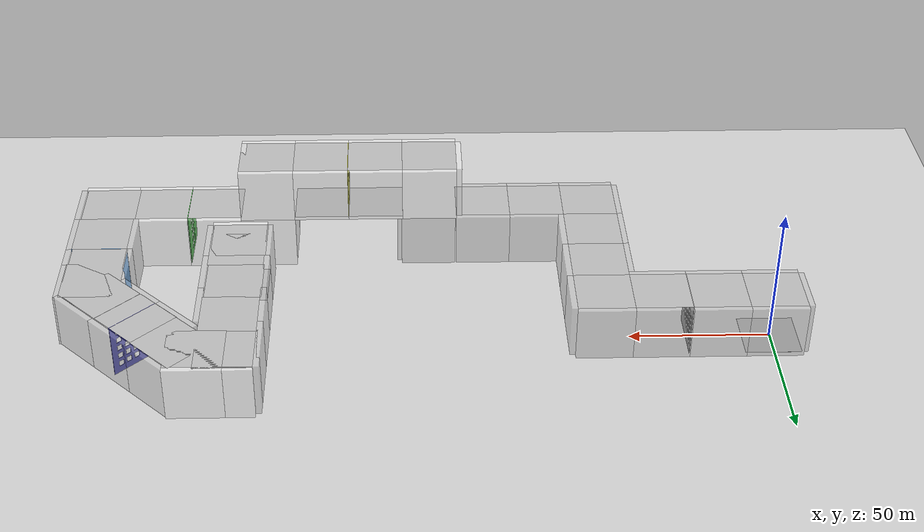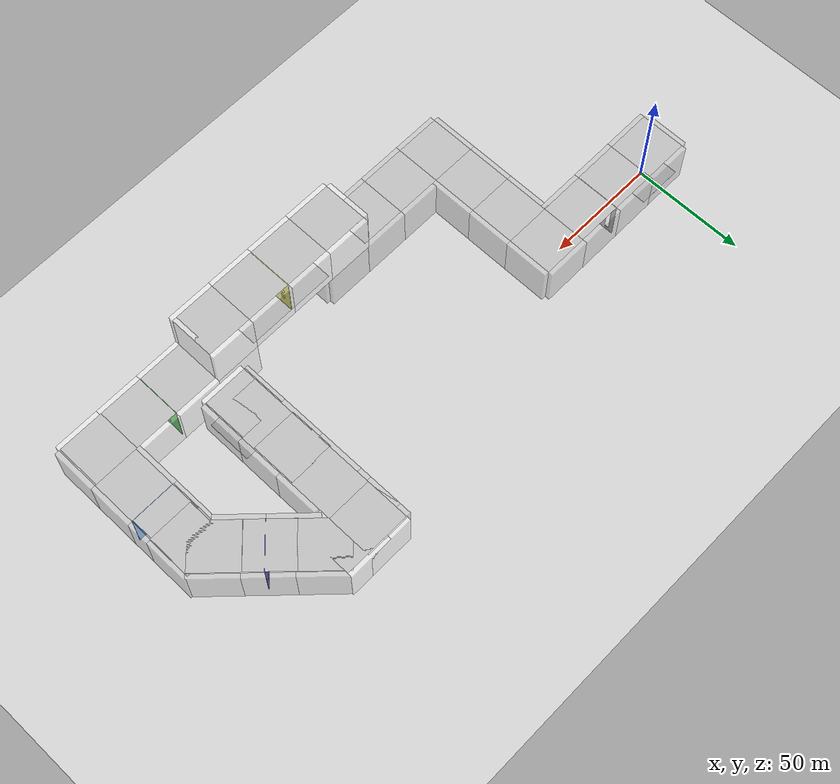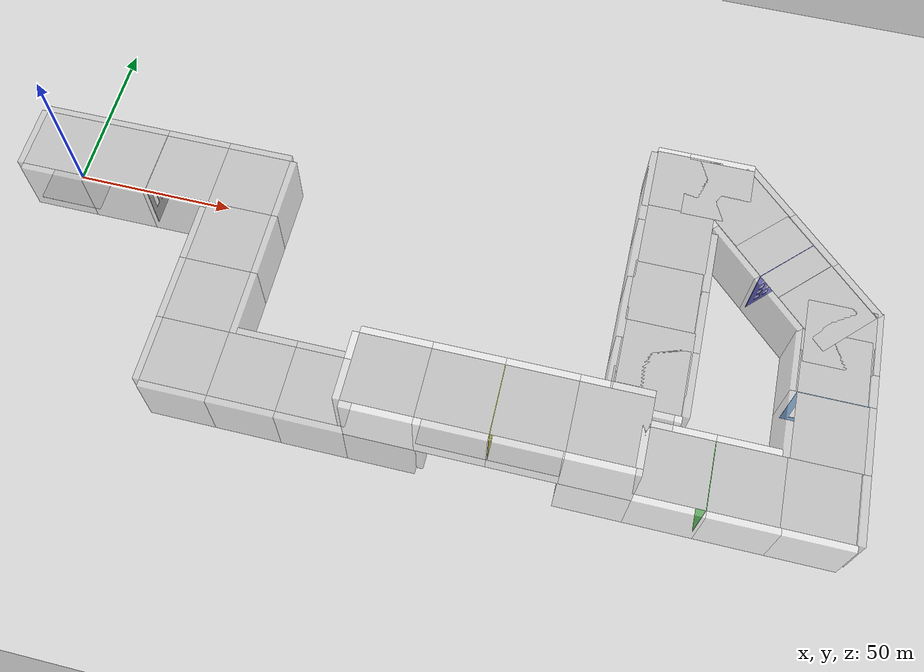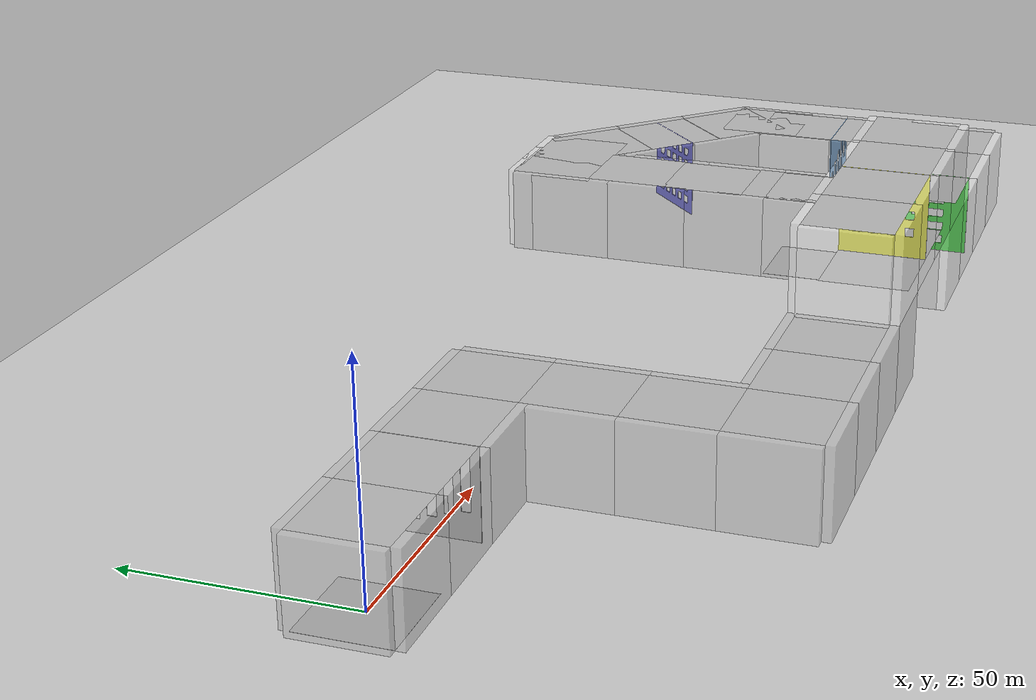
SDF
<sdf version="1.5">
 <world name="default">
  <scene>
   <ambient>0.8 0.8 0.8 1.0</ambient>
   <grid>false</grid>
   <shadows>true</shadows>
   <sky><clouds><speed>12</speed></clouds></sky>
  </scene>
  <include><uri>model://race2new</uri></include>
  <include><uri>model://grass_plane</uri></include>
  <include><uri>model://barycenter</uri></include>
  <include><uri>model://partition_13</uri><pose>30 0 0 0 0 -1.574</pose></include>
  <include><uri>model://partition_1</uri><pose>150 -60 20 0 0 1.574</pose></include>
  <include><uri>model://partition_2</uri><pose>210 -60 0 0 0 -1.574</pose></include>
  <include><uri>model://partition_12</uri><pose>240 -30 0 0 0 0</pose></include>
  <include><uri>model://partition_11</uri><pose>222.9 11 0 0 0 0.785</pose></include>
  <include><uri>model://start_place</uri><pose>0 0 0.05 0 0 0</pose></include>
  <include><uri>model://finish_place</uri><pose>190 -35 0.05 0 0 0</pose></include>
  <light name="user_spot_light_0" type="spot">
   <pose>0 0 200 0 -0 0</pose>
   <diffuse>0.9 0.9 0.9 1</diffuse>
   <specular>0.3 0.3 0.3 1</specular>
   <direction>0 0 -1</direction>
   <attenuation>
    <range>400</range>
    <constant>0.003</constant>
    <linear>0.0003</linear>
    <quadratic>0.00003</quadratic>
   </attenuation>
   <cast_shadows>0</cast_shadows>
   <spot><inner_angle>1.9</inner_angle><outer_angle>2.1</outer_angle><falloff>1</falloff></spot>
  </light>
  <light name="user_spot_light_1" type="spot">
   <pose>200 20 200 0 -0 0</pose>
   <diffuse>0.9 0.9 0.9 1</diffuse>
   <specular>0.3 0.3 0.3 1</specular>
   <direction>0 0 -1</direction>
   <attenuation>
    <range>400</range>
    <constant>0.003</constant>
    <linear>0.0003</linear>
    <quadratic>0.00003</quadratic>
   </attenuation>
   <cast_shadows>0</cast_shadows>
   <spot><inner_angle>1.9</inner_angle><outer_angle>2.1</outer_angle><falloff>1</falloff></spot>
  </light>
  <physics name="default_physics" default="0" type="ode">
   <gravity>0 0 -9.8066</gravity>
   <ode>
    <solver>
     <type>quick</type>
     <iters>10</iters>
     <sor>1.3</sor>
     <use_dynamic_moi_rescaling>0</use_dynamic_moi_rescaling>
    </solver>
    <constraints>
     <cfm>0</cfm>
     <erp>0.2</erp>
     <contact_max_correcting_vel>100</contact_max_correcting_vel>
     <contact_surface_layer>0.001</contact_surface_layer>
    </constraints>
   </ode>
   <max_step_size>0.004</max_step_size>
   <real_time_factor>1</real_time_factor>
   <real_time_update_rate>250</real_time_update_rate>
   <magnetic_field>6e-06 2.3e-05 -4.2e-05</magnetic_field>
  </physics>
 </world>
</sdf>

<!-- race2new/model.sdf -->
<sdf version='1.7'>
  <model name='race2'>
    <link name='link'>
      <self_collide>0</self_collide>
      <enable_wind>0</enable_wind>
      <kinematic>0</kinematic>
      <pose>0 11 10 -1.5708 0 0</pose>
      <visual name='visual'>
        <cast_shadows>1</cast_shadows>
        <transparency>0.6</transparency>
        <geometry>
          <box>
            <size>20 20 2</size>
          </box>
        </geometry>
        <material>
          <script>
            <uri>model://new_wall/materials/scripts</uri>
            <uri>model://new_wall/materials/textures/</uri>
            <name>NewWall/Image</name>
          </script>
          <shader type='pixel'/>
        </material>
        <pose>0 0 0 0 -0 0</pose>
      </visual>
      <collision name='collision'>
        <laser_retro>0</laser_retro>
        <max_contacts>10</max_contacts>
        <pose>0 0 0 0 -0 0</pose>
        <geometry>
          <box>
            <size>20 20 2</size>
          </box>
        </geometry>
        <surface>
          <friction>
            <ode>
              <mu>100</mu>
              <mu2>50</mu2>
              <fdir1>0 0 0</fdir1>
              <slip1>0</slip1>
              <slip2>0</slip2>
            </ode>
            <torsional>
              <coefficient>1</coefficient>
              <patch_radius>0</patch_radius>
              <surface_radius>0</surface_radius>
              <use_patch_radius>1</use_patch_radius>
              <ode>
                <slip>0</slip>
              </ode>
            </torsional>
          </friction>
          <bounce>
            <restitution_coefficient>0</restitution_coefficient>
            <threshold>1e+06</threshold>
          </bounce>
          <contact>
            <collide_without_contact>0</collide_without_contact>
            <collide_without_contact_bitmask>1</collide_without_contact_bitmask>
            <collide_bitmask>1</collide_bitmask>
            <ode>
              <soft_cfm>0</soft_cfm>
              <soft_erp>0.2</soft_erp>
              <kp>1e+13</kp>
              <kd>1</kd>
              <max_vel>0.01</max_vel>
              <min_depth>0</min_depth>
            </ode>
            <bullet>
              <split_impulse>1</split_impulse>
              <split_impulse_penetration_threshold>-0.01</split_impulse_penetration_threshold>
              <soft_cfm>0</soft_cfm>
              <soft_erp>0.2</soft_erp>
              <kp>1e+13</kp>
              <kd>1</kd>
            </bullet>
          </contact>
        </surface>
      </collision>
    </link>
    <link name='link_clone'>
      <self_collide>0</self_collide>
      <enable_wind>0</enable_wind>
      <kinematic>0</kinematic>
      <pose>0 -11 10 -1.5708 0 0</pose>
      <visual name='visual'>
        <cast_shadows>1</cast_shadows>
        <transparency>0.6</transparency>
        <geometry>
          <box>
            <size>20 20 2</size>
          </box>
        </geometry>
        <material>
          <script>
            <uri>model://new_wall/materials/scripts</uri>
            <uri>model://new_wall/materials/textures/</uri>
            <name>NewWall/Image</name>
          </script>
          <shader type='pixel'/>
        </material>
        <pose>0 0 0 0 -0 0</pose>
      </visual>
      <collision name='collision'>
        <laser_retro>0</laser_retro>
        <max_contacts>10</max_contacts>
        <pose>0 0 0 0 -0 0</pose>
        <geometry>
          <box>
            <size>20 20 2</size>
          </box>
        </geometry>
        <surface>
          <friction>
            <ode>
              <mu>1</mu>
              <mu2>1</mu2>
              <fdir1>0 0 0</fdir1>
              <slip1>0</slip1>
              <slip2>0</slip2>
            </ode>
            <torsional>
              <coefficient>1</coefficient>
              <patch_radius>0</patch_radius>
              <surface_radius>0</surface_radius>
              <use_patch_radius>1</use_patch_radius>
              <ode>
                <slip>0</slip>
              </ode>
            </torsional>
          </friction>
          <bounce>
            <restitution_coefficient>0</restitution_coefficient>
            <threshold>1e+06</threshold>
          </bounce>
          <contact>
            <collide_without_contact>0</collide_without_contact>
            <collide_without_contact_bitmask>1</collide_without_contact_bitmask>
            <collide_bitmask>1</collide_bitmask>
            <ode>
              <soft_cfm>0</soft_cfm>
              <soft_erp>0.2</soft_erp>
              <kp>1e+13</kp>
              <kd>1</kd>
              <max_vel>0.01</max_vel>
              <min_depth>0</min_depth>
            </ode>
            <bullet>
              <split_impulse>1</split_impulse>
              <split_impulse_penetration_threshold>-0.01</split_impulse_penetration_threshold>
              <soft_cfm>0</soft_cfm>
              <soft_erp>0.2</soft_erp>
              <kp>1e+13</kp>
              <kd>1</kd>
            </bullet>
          </contact>
        </surface>
      </collision>
    </link>
    <link name='link_clone_0'>
      <self_collide>0</self_collide>
      <enable_wind>0</enable_wind>
      <kinematic>0</kinematic>
      <pose>-11 0 10 -1.5708 4e-06 1.5708</pose>
      <visual name='visual'>
        <cast_shadows>1</cast_shadows>
        <transparency>0.6</transparency>
        <geometry>
          <box>
            <size>20 20 2</size>
          </box>
        </geometry>
        <material>
          <script>
            <uri>model://new_wall/materials/scripts</uri>
            <uri>model://new_wall/materials/textures/</uri>
            <name>NewWall/Image</name>
          </script>
          <shader type='pixel'/>
        </material>
        <pose>0 0 0 0 -0 0</pose>
      </visual>
      <collision name='collision'>
        <laser_retro>0</laser_retro>
        <max_contacts>10</max_contacts>
        <pose>0 0 0 0 -0 0</pose>
        <geometry>
          <box>
            <size>20 20 2</size>
          </box>
        </geometry>
        <surface>
          <friction>
            <ode>
              <mu>1</mu>
              <mu2>1</mu2>
              <fdir1>0 0 0</fdir1>
              <slip1>0</slip1>
              <slip2>0</slip2>
            </ode>
            <torsional>
              <coefficient>1</coefficient>
              <patch_radius>0</patch_radius>
              <surface_radius>0</surface_radius>
              <use_patch_radius>1</use_patch_radius>
              <ode>
                <slip>0</slip>
              </ode>
            </torsional>
          </friction>
          <bounce>
            <restitution_coefficient>0</restitution_coefficient>
            <threshold>1e+06</threshold>
          </bounce>
          <contact>
            <collide_without_contact>0</collide_without_contact>
            <collide_without_contact_bitmask>1</collide_without_contact_bitmask>
            <collide_bitmask>1</collide_bitmask>
            <ode>
              <soft_cfm>0</soft_cfm>
              <soft_erp>0.2</soft_erp>
              <kp>1e+13</kp>
              <kd>1</kd>
              <max_vel>0.01</max_vel>
              <min_depth>0</min_depth>
            </ode>
            <bullet>
              <split_impulse>1</split_impulse>
              <split_impulse_penetration_threshold>-0.01</split_impulse_penetration_threshold>
              <soft_cfm>0</soft_cfm>
              <soft_erp>0.2</soft_erp>
              <kp>1e+13</kp>
              <kd>1</kd>
            </bullet>
          </contact>
        </surface>
      </collision>
    </link>
    <link name='link_clone_0_clone'>
      <self_collide>0</self_collide>
      <enable_wind>0</enable_wind>
      <kinematic>0</kinematic>
      <pose>49 -20 10 -1.5708 4e-06 1.5708</pose>
      <visual name='visual'>
        <cast_shadows>1</cast_shadows>
        <transparency>0.6</transparency>
        <geometry>
          <box>
            <size>20 20 2</size>
          </box>
        </geometry>
        <material>
          <script>
            <uri>model://new_wall/materials/scripts</uri>
            <uri>model://new_wall/materials/textures/</uri>
            <name>NewWall/Image</name>
          </script>
          <shader type='pixel'/>
        </material>
        <pose>0 0 0 0 -0 0</pose>
      </visual>
      <collision name='collision'>
        <laser_retro>0</laser_retro>
        <max_contacts>10</max_contacts>
        <pose>0 0 0 0 -0 0</pose>
        <geometry>
          <box>
            <size>20 20 2</size>
          </box>
        </geometry>
        <surface>
          <friction>
            <ode>
              <mu>1</mu>
              <mu2>1</mu2>
              <fdir1>0 0 0</fdir1>
              <slip1>0</slip1>
              <slip2>0</slip2>
            </ode>
            <torsional>
              <coefficient>1</coefficient>
              <patch_radius>0</patch_radius>
              <surface_radius>0</surface_radius>
              <use_patch_radius>1</use_patch_radius>
              <ode>
                <slip>0</slip>
              </ode>
            </torsional>
          </friction>
          <bounce>
            <restitution_coefficient>0</restitution_coefficient>
            <threshold>1e+06</threshold>
          </bounce>
          <contact>
            <collide_without_contact>0</collide_without_contact>
            <collide_without_contact_bitmask>1</collide_without_contact_bitmask>
            <collide_bitmask>1</collide_bitmask>
            <ode>
              <soft_cfm>0</soft_cfm>
              <soft_erp>0.2</soft_erp>
              <kp>1e+13</kp>
              <kd>1</kd>
              <max_vel>0.01</max_vel>
              <min_depth>0</min_depth>
            </ode>
            <bullet>
              <split_impulse>1</split_impulse>
              <split_impulse_penetration_threshold>-0.01</split_impulse_penetration_threshold>
              <soft_cfm>0</soft_cfm>
              <soft_erp>0.2</soft_erp>
              <kp>1e+13</kp>
              <kd>1</kd>
            </bullet>
          </contact>
        </surface>
      </collision>
    </link>
    <link name='link_clone_0_clone_0'>
      <self_collide>0</self_collide>
      <enable_wind>0</enable_wind>
      <kinematic>0</kinematic>
      <pose>71 0 10 -1.5708 4e-06 1.5708</pose>
      <visual name='visual'>
        <cast_shadows>1</cast_shadows>
        <transparency>0.6</transparency>
        <geometry>
          <box>
            <size>20 20 2</size>
          </box>
        </geometry>
        <material>
          <script>
            <uri>model://new_wall/materials/scripts</uri>
            <uri>model://new_wall/materials/textures/</uri>
            <name>NewWall/Image</name>
          </script>
          <shader type='pixel'/>
        </material>
        <pose>0 0 0 0 -0 0</pose>
      </visual>
      <collision name='collision'>
        <laser_retro>0</laser_retro>
        <max_contacts>10</max_contacts>
        <pose>0 0 0 0 -0 0</pose>
        <geometry>
          <box>
            <size>20 20 2</size>
          </box>
        </geometry>
        <surface>
          <friction>
            <ode>
              <mu>1</mu>
              <mu2>1</mu2>
              <fdir1>0 0 0</fdir1>
              <slip1>0</slip1>
              <slip2>0</slip2>
            </ode>
            <torsional>
              <coefficient>1</coefficient>
              <patch_radius>0</patch_radius>
              <surface_radius>0</surface_radius>
              <use_patch_radius>1</use_patch_radius>
              <ode>
                <slip>0</slip>
              </ode>
            </torsional>
          </friction>
          <bounce>
            <restitution_coefficient>0</restitution_coefficient>
            <threshold>1e+06</threshold>
          </bounce>
          <contact>
            <collide_without_contact>0</collide_without_contact>
            <collide_without_contact_bitmask>1</collide_without_contact_bitmask>
            <collide_bitmask>1</collide_bitmask>
            <ode>
              <soft_cfm>0</soft_cfm>
              <soft_erp>0.2</soft_erp>
              <kp>1e+13</kp>
              <kd>1</kd>
              <max_vel>0.01</max_vel>
              <min_depth>0</min_depth>
            </ode>
            <bullet>
              <split_impulse>1</split_impulse>
              <split_impulse_penetration_threshold>-0.01</split_impulse_penetration_threshold>
              <soft_cfm>0</soft_cfm>
              <soft_erp>0.2</soft_erp>
              <kp>1e+13</kp>
              <kd>1</kd>
            </bullet>
          </contact>
        </surface>
      </collision>
    </link>
    <link name='link_clone_0_clone_1'>
      <self_collide>0</self_collide>
      <enable_wind>0</enable_wind>
      <kinematic>0</kinematic>
      <pose>71 -20 10 -1.5708 4e-06 1.5708</pose>
      <visual name='visual'>
        <cast_shadows>1</cast_shadows>
        <transparency>0.6</transparency>
        <geometry>
          <box>
            <size>20 20 2</size>
          </box>
        </geometry>
        <material>
          <script>
            <uri>model://new_wall/materials/scripts</uri>
            <uri>model://new_wall/materials/textures/</uri>
            <name>NewWall/Image</name>
          </script>
          <shader type='pixel'/>
        </material>
        <pose>0 0 0 0 -0 0</pose>
      </visual>
      <collision name='collision'>
        <laser_retro>0</laser_retro>
        <max_contacts>10</max_contacts>
        <pose>0 0 0 0 -0 0</pose>
        <geometry>
          <box>
            <size>20 20 2</size>
          </box>
        </geometry>
        <surface>
          <friction>
            <ode>
              <mu>1</mu>
              <mu2>1</mu2>
              <fdir1>0 0 0</fdir1>
              <slip1>0</slip1>
              <slip2>0</slip2>
            </ode>
            <torsional>
              <coefficient>1</coefficient>
              <patch_radius>0</patch_radius>
              <surface_radius>0</surface_radius>
              <use_patch_radius>1</use_patch_radius>
              <ode>
                <slip>0</slip>
              </ode>
            </torsional>
          </friction>
          <bounce>
            <restitution_coefficient>0</restitution_coefficient>
            <threshold>1e+06</threshold>
          </bounce>
          <contact>
            <collide_without_contact>0</collide_without_contact>
            <collide_without_contact_bitmask>1</collide_without_contact_bitmask>
            <collide_bitmask>1</collide_bitmask>
            <ode>
              <soft_cfm>0</soft_cfm>
              <soft_erp>0.2</soft_erp>
              <kp>1e+13</kp>
              <kd>1</kd>
              <max_vel>0.01</max_vel>
              <min_depth>0</min_depth>
            </ode>
            <bullet>
              <split_impulse>1</split_impulse>
              <split_impulse_penetration_threshold>-0.01</split_impulse_penetration_threshold>
              <soft_cfm>0</soft_cfm>
              <soft_erp>0.2</soft_erp>
              <kp>1e+13</kp>
              <kd>1</kd>
            </bullet>
          </contact>
        </surface>
      </collision>
    </link>
    <link name='link_clone_0_clone_2'>
      <self_collide>0</self_collide>
      <enable_wind>0</enable_wind>
      <kinematic>0</kinematic>
      <pose>71 -40 10 -1.5708 4e-06 1.5708</pose>
      <visual name='visual'>
        <cast_shadows>1</cast_shadows>
        <transparency>0.6</transparency>
        <geometry>
          <box>
            <size>20 20 2</size>
          </box>
        </geometry>
        <material>
          <script>
            <uri>model://new_wall/materials/scripts</uri>
            <uri>model://new_wall/materials/textures/</uri>
            <name>NewWall/Image</name>
          </script>
          <shader type='pixel'/>
        </material>
        <pose>0 0 0 0 -0 0</pose>
      </visual>
      <collision name='collision'>
        <laser_retro>0</laser_retro>
        <max_contacts>10</max_contacts>
        <pose>0 0 0 0 -0 0</pose>
        <geometry>
          <box>
            <size>20 20 2</size>
          </box>
        </geometry>
        <surface>
          <friction>
            <ode>
              <mu>1</mu>
              <mu2>1</mu2>
              <fdir1>0 0 0</fdir1>
              <slip1>0</slip1>
              <slip2>0</slip2>
            </ode>
            <torsional>
              <coefficient>1</coefficient>
              <patch_radius>0</patch_radius>
              <surface_radius>0</surface_radius>
              <use_patch_radius>1</use_patch_radius>
              <ode>
                <slip>0</slip>
              </ode>
            </torsional>
          </friction>
          <bounce>
            <restitution_coefficient>0</restitution_coefficient>
            <threshold>1e+06</threshold>
          </bounce>
          <contact>
            <collide_without_contact>0</collide_without_contact>
            <collide_without_contact_bitmask>1</collide_without_contact_bitmask>
            <collide_bitmask>1</collide_bitmask>
            <ode>
              <soft_cfm>0</soft_cfm>
              <soft_erp>0.2</soft_erp>
              <kp>1e+13</kp>
              <kd>1</kd>
              <max_vel>0.01</max_vel>
              <min_depth>0</min_depth>
            </ode>
            <bullet>
              <split_impulse>1</split_impulse>
              <split_impulse_penetration_threshold>-0.01</split_impulse_penetration_threshold>
              <soft_cfm>0</soft_cfm>
              <soft_erp>0.2</soft_erp>
              <kp>1e+13</kp>
              <kd>1</kd>
            </bullet>
          </contact>
        </surface>
      </collision>
    </link>
    <link name='link_clone_0_clone_3'>
      <self_collide>0</self_collide>
      <enable_wind>0</enable_wind>
      <kinematic>0</kinematic>
      <pose>49 -40 10 -1.5708 4e-06 1.5708</pose>
      <visual name='visual'>
        <cast_shadows>1</cast_shadows>
        <transparency>0.6</transparency>
        <geometry>
          <box>
            <size>20 20 2</size>
          </box>
        </geometry>
        <material>
          <script>
            <uri>model://new_wall/materials/scripts</uri>
            <uri>model://new_wall/materials/textures/</uri>
            <name>NewWall/Image</name>
          </script>
          <shader type='pixel'/>
        </material>
        <pose>0 0 0 0 -0 0</pose>
      </visual>
      <collision name='collision'>
        <laser_retro>0</laser_retro>
        <max_contacts>10</max_contacts>
        <pose>0 0 0 0 -0 0</pose>
        <geometry>
          <box>
            <size>20 20 2</size>
          </box>
        </geometry>
        <surface>
          <friction>
            <ode>
              <mu>1</mu>
              <mu2>1</mu2>
              <fdir1>0 0 0</fdir1>
              <slip1>0</slip1>
              <slip2>0</slip2>
            </ode>
            <torsional>
              <coefficient>1</coefficient>
              <patch_radius>0</patch_radius>
              <surface_radius>0</surface_radius>
              <use_patch_radius>1</use_patch_radius>
              <ode>
                <slip>0</slip>
              </ode>
            </torsional>
          </friction>
          <bounce>
            <restitution_coefficient>0</restitution_coefficient>
            <threshold>1e+06</threshold>
          </bounce>
          <contact>
            <collide_without_contact>0</collide_without_contact>
            <collide_without_contact_bitmask>1</collide_without_contact_bitmask>
            <collide_bitmask>1</collide_bitmask>
            <ode>
              <soft_cfm>0</soft_cfm>
              <soft_erp>0.2</soft_erp>
              <kp>1e+13</kp>
              <kd>1</kd>
              <max_vel>0.01</max_vel>
              <min_depth>0</min_depth>
            </ode>
            <bullet>
              <split_impulse>1</split_impulse>
              <split_impulse_penetration_threshold>-0.01</split_impulse_penetration_threshold>
              <soft_cfm>0</soft_cfm>
              <soft_erp>0.2</soft_erp>
              <kp>1e+13</kp>
              <kd>1</kd>
            </bullet>
          </contact>
        </surface>
      </collision>
    </link>
    <link name='link_clone_0_clone_4'>
      <self_collide>0</self_collide>
      <enable_wind>0</enable_wind>
      <kinematic>0</kinematic>
      <pose>49 -60 10 -1.5708 4e-06 1.5708</pose>
      <visual name='visual'>
        <cast_shadows>1</cast_shadows>
        <transparency>0.6</transparency>
        <geometry>
          <box>
            <size>20 20 2</size>
          </box>
        </geometry>
        <material>
          <script>
            <uri>model://new_wall/materials/scripts</uri>
            <uri>model://new_wall/materials/textures/</uri>
            <name>NewWall/Image</name>
          </script>
          <shader type='pixel'/>
        </material>
        <pose>0 0 0 0 -0 0</pose>
      </visual>
      <collision name='collision'>
        <laser_retro>0</laser_retro>
        <max_contacts>10</max_contacts>
        <pose>0 0 0 0 -0 0</pose>
        <geometry>
          <box>
            <size>20 20 2</size>
          </box>
        </geometry>
        <surface>
          <friction>
            <ode>
              <mu>1</mu>
              <mu2>1</mu2>
              <fdir1>0 0 0</fdir1>
              <slip1>0</slip1>
              <slip2>0</slip2>
            </ode>
            <torsional>
              <coefficient>1</coefficient>
              <patch_radius>0</patch_radius>
              <surface_radius>0</surface_radius>
              <use_patch_radius>1</use_patch_radius>
              <ode>
                <slip>0</slip>
              </ode>
            </torsional>
          </friction>
          <bounce>
            <restitution_coefficient>0</restitution_coefficient>
            <threshold>1e+06</threshold>
          </bounce>
          <contact>
            <collide_without_contact>0</collide_without_contact>
            <collide_without_contact_bitmask>1</collide_without_contact_bitmask>
            <collide_bitmask>1</collide_bitmask>
            <ode>
              <soft_cfm>0</soft_cfm>
              <soft_erp>0.2</soft_erp>
              <kp>1e+13</kp>
              <kd>1</kd>
              <max_vel>0.01</max_vel>
              <min_depth>0</min_depth>
            </ode>
            <bullet>
              <split_impulse>1</split_impulse>
              <split_impulse_penetration_threshold>-0.01</split_impulse_penetration_threshold>
              <soft_cfm>0</soft_cfm>
              <soft_erp>0.2</soft_erp>
              <kp>1e+13</kp>
              <kd>1</kd>
            </bullet>
          </contact>
        </surface>
      </collision>
    </link>
    <link name='link_clone_0_clone_4_clone'>
      <self_collide>0</self_collide>
      <enable_wind>0</enable_wind>
      <kinematic>0</kinematic>
      <pose>131 -60 10 -1.5708 4e-06 1.5708</pose>
      <visual name='visual'>
        <cast_shadows>1</cast_shadows>
        <transparency>0.6</transparency>
        <geometry>
          <box>
            <size>20 20 2</size>
          </box>
        </geometry>
        <material>
          <script>
            <uri>model://new_wall/materials/scripts</uri>
            <uri>model://new_wall/materials/textures/</uri>
            <name>NewWall/Image</name>
          </script>
          <shader type='pixel'/>
        </material>
        <pose>0 0 0 0 -0 0</pose>
      </visual>
      <collision name='collision'>
        <laser_retro>0</laser_retro>
        <max_contacts>10</max_contacts>
        <pose>0 0 0 0 -0 0</pose>
        <geometry>
          <box>
            <size>20 20 2</size>
          </box>
        </geometry>
        <surface>
          <friction>
            <ode>
              <mu>1</mu>
              <mu2>1</mu2>
              <fdir1>0 0 0</fdir1>
              <slip1>0</slip1>
              <slip2>0</slip2>
            </ode>
            <torsional>
              <coefficient>1</coefficient>
              <patch_radius>0</patch_radius>
              <surface_radius>0</surface_radius>
              <use_patch_radius>1</use_patch_radius>
              <ode>
                <slip>0</slip>
              </ode>
            </torsional>
          </friction>
          <bounce>
            <restitution_coefficient>0</restitution_coefficient>
            <threshold>1e+06</threshold>
          </bounce>
          <contact>
            <collide_without_contact>0</collide_without_contact>
            <collide_without_contact_bitmask>1</collide_without_contact_bitmask>
            <collide_bitmask>1</collide_bitmask>
            <ode>
              <soft_cfm>0</soft_cfm>
              <soft_erp>0.2</soft_erp>
              <kp>1e+13</kp>
              <kd>1</kd>
              <max_vel>0.01</max_vel>
              <min_depth>0</min_depth>
            </ode>
            <bullet>
              <split_impulse>1</split_impulse>
              <split_impulse_penetration_threshold>-0.01</split_impulse_penetration_threshold>
              <soft_cfm>0</soft_cfm>
              <soft_erp>0.2</soft_erp>
              <kp>1e+13</kp>
              <kd>1</kd>
            </bullet>
          </contact>
        </surface>
      </collision>
    </link>
    <link name='link_clone_0_clone_4_clone_clone'>
      <self_collide>0</self_collide>
      <enable_wind>0</enable_wind>
      <kinematic>0</kinematic>
      <pose>171 -60 10 -1.5708 4e-06 1.5708</pose>
      <visual name='visual'>
        <cast_shadows>1</cast_shadows>
        <transparency>0.6</transparency>
        <geometry>
          <box>
            <size>20 20 2</size>
          </box>
        </geometry>
        <material>
          <script>
            <uri>model://new_wall/materials/scripts</uri>
            <uri>model://new_wall/materials/textures/</uri>
            <name>NewWall/Image</name>
          </script>
          <shader type='pixel'/>
        </material>
        <pose>0 0 0 0 -0 0</pose>
      </visual>
      <collision name='collision'>
        <laser_retro>0</laser_retro>
        <max_contacts>10</max_contacts>
        <pose>0 0 0 0 -0 0</pose>
        <geometry>
          <box>
            <size>20 20 2</size>
          </box>
        </geometry>
        <surface>
          <friction>
            <ode>
              <mu>1</mu>
              <mu2>1</mu2>
              <fdir1>0 0 0</fdir1>
              <slip1>0</slip1>
              <slip2>0</slip2>
            </ode>
            <torsional>
              <coefficient>1</coefficient>
              <patch_radius>0</patch_radius>
              <surface_radius>0</surface_radius>
              <use_patch_radius>1</use_patch_radius>
              <ode>
                <slip>0</slip>
              </ode>
            </torsional>
          </friction>
          <bounce>
            <restitution_coefficient>0</restitution_coefficient>
            <threshold>1e+06</threshold>
          </bounce>
          <contact>
            <collide_without_contact>0</collide_without_contact>
            <collide_without_contact_bitmask>1</collide_without_contact_bitmask>
            <collide_bitmask>1</collide_bitmask>
            <ode>
              <soft_cfm>0</soft_cfm>
              <soft_erp>0.2</soft_erp>
              <kp>1e+13</kp>
              <kd>1</kd>
              <max_vel>0.01</max_vel>
              <min_depth>0</min_depth>
            </ode>
            <bullet>
              <split_impulse>1</split_impulse>
              <split_impulse_penetration_threshold>-0.01</split_impulse_penetration_threshold>
              <soft_cfm>0</soft_cfm>
              <soft_erp>0.2</soft_erp>
              <kp>1e+13</kp>
              <kd>1</kd>
            </bullet>
          </contact>
        </surface>
      </collision>
    </link>
    <link name='link_clone_0_clone_4_clone_clone_0'>
      <self_collide>0</self_collide>
      <enable_wind>0</enable_wind>
      <kinematic>0</kinematic>
      <pose>251 -60 10 -1.5708 4e-06 1.5708</pose>
      <visual name='visual'>
        <cast_shadows>1</cast_shadows>
        <transparency>0.6</transparency>
        <geometry>
          <box>
            <size>20 20 2</size>
          </box>
        </geometry>
        <material>
          <script>
            <uri>model://new_wall/materials/scripts</uri>
            <uri>model://new_wall/materials/textures/</uri>
            <name>NewWall/Image</name>
          </script>
          <shader type='pixel'/>
        </material>
        <pose>0 0 0 0 -0 0</pose>
      </visual>
      <collision name='collision'>
        <laser_retro>0</laser_retro>
        <max_contacts>10</max_contacts>
        <pose>0 0 0 0 -0 0</pose>
        <geometry>
          <box>
            <size>20 20 2</size>
          </box>
        </geometry>
        <surface>
          <friction>
            <ode>
              <mu>1</mu>
              <mu2>1</mu2>
              <fdir1>0 0 0</fdir1>
              <slip1>0</slip1>
              <slip2>0</slip2>
            </ode>
            <torsional>
              <coefficient>1</coefficient>
              <patch_radius>0</patch_radius>
              <surface_radius>0</surface_radius>
              <use_patch_radius>1</use_patch_radius>
              <ode>
                <slip>0</slip>
              </ode>
            </torsional>
          </friction>
          <bounce>
            <restitution_coefficient>0</restitution_coefficient>
            <threshold>1e+06</threshold>
          </bounce>
          <contact>
            <collide_without_contact>0</collide_without_contact>
            <collide_without_contact_bitmask>1</collide_without_contact_bitmask>
            <collide_bitmask>1</collide_bitmask>
            <ode>
              <soft_cfm>0</soft_cfm>
              <soft_erp>0.2</soft_erp>
              <kp>1e+13</kp>
              <kd>1</kd>
              <max_vel>0.01</max_vel>
              <min_depth>0</min_depth>
            </ode>
            <bullet>
              <split_impulse>1</split_impulse>
              <split_impulse_penetration_threshold>-0.01</split_impulse_penetration_threshold>
              <soft_cfm>0</soft_cfm>
              <soft_erp>0.2</soft_erp>
              <kp>1e+13</kp>
              <kd>1</kd>
            </bullet>
          </contact>
        </surface>
      </collision>
    </link>
    <link name='link_clone_0_clone_4_clone_clone_0_clone'>
      <self_collide>0</self_collide>
      <enable_wind>0</enable_wind>
      <kinematic>0</kinematic>
      <pose>229 -40 10 -1.5708 4e-06 1.5708</pose>
      <visual name='visual'>
        <cast_shadows>1</cast_shadows>
        <transparency>0.6</transparency>
        <geometry>
          <box>
            <size>20 20 2</size>
          </box>
        </geometry>
        <material>
          <script>
            <uri>model://new_wall/materials/scripts</uri>
            <uri>model://new_wall/materials/textures/</uri>
            <name>NewWall/Image</name>
          </script>
          <shader type='pixel'/>
        </material>
        <pose>0 0 0 0 -0 0</pose>
      </visual>
      <collision name='collision'>
        <laser_retro>0</laser_retro>
        <max_contacts>10</max_contacts>
        <pose>0 0 0 0 -0 0</pose>
        <geometry>
          <box>
            <size>20 20 2</size>
          </box>
        </geometry>
        <surface>
          <friction>
            <ode>
              <mu>1</mu>
              <mu2>1</mu2>
              <fdir1>0 0 0</fdir1>
              <slip1>0</slip1>
              <slip2>0</slip2>
            </ode>
            <torsional>
              <coefficient>1</coefficient>
              <patch_radius>0</patch_radius>
              <surface_radius>0</surface_radius>
              <use_patch_radius>1</use_patch_radius>
              <ode>
                <slip>0</slip>
              </ode>
            </torsional>
          </friction>
          <bounce>
            <restitution_coefficient>0</restitution_coefficient>
            <threshold>1e+06</threshold>
          </bounce>
          <contact>
            <collide_without_contact>0</collide_without_contact>
            <collide_without_contact_bitmask>1</collide_without_contact_bitmask>
            <collide_bitmask>1</collide_bitmask>
            <ode>
              <soft_cfm>0</soft_cfm>
              <soft_erp>0.2</soft_erp>
              <kp>1e+13</kp>
              <kd>1</kd>
              <max_vel>0.01</max_vel>
              <min_depth>0</min_depth>
            </ode>
            <bullet>
              <split_impulse>1</split_impulse>
              <split_impulse_penetration_threshold>-0.01</split_impulse_penetration_threshold>
              <soft_cfm>0</soft_cfm>
              <soft_erp>0.2</soft_erp>
              <kp>1e+13</kp>
              <kd>1</kd>
            </bullet>
          </contact>
        </surface>
      </collision>
    </link>
    <link name='link_clone_0_clone_4_clone_clone_0_clone_clone'>
      <self_collide>0</self_collide>
      <enable_wind>0</enable_wind>
      <kinematic>0</kinematic>
      <pose>229 -20 10 -1.5708 4e-06 1.5708</pose>
      <visual name='visual'>
        <cast_shadows>1</cast_shadows>
        <transparency>0.6</transparency>
        <geometry>
          <box>
            <size>20 20 2</size>
          </box>
        </geometry>
        <material>
          <script>
            <uri>model://new_wall/materials/scripts</uri>
            <uri>model://new_wall/materials/textures/</uri>
            <name>NewWall/Image</name>
          </script>
          <shader type='pixel'/>
        </material>
        <pose>0 0 0 0 -0 0</pose>
      </visual>
      <collision name='collision'>
        <laser_retro>0</laser_retro>
        <max_contacts>10</max_contacts>
        <pose>0 0 0 0 -0 0</pose>
        <geometry>
          <box>
            <size>20 20 2</size>
          </box>
        </geometry>
        <surface>
          <friction>
            <ode>
              <mu>1</mu>
              <mu2>1</mu2>
              <fdir1>0 0 0</fdir1>
              <slip1>0</slip1>
              <slip2>0</slip2>
            </ode>
            <torsional>
              <coefficient>1</coefficient>
              <patch_radius>0</patch_radius>
              <surface_radius>0</surface_radius>
              <use_patch_radius>1</use_patch_radius>
              <ode>
                <slip>0</slip>
              </ode>
            </torsional>
          </friction>
          <bounce>
            <restitution_coefficient>0</restitution_coefficient>
            <threshold>1e+06</threshold>
          </bounce>
          <contact>
            <collide_without_contact>0</collide_without_contact>
            <collide_without_contact_bitmask>1</collide_without_contact_bitmask>
            <collide_bitmask>1</collide_bitmask>
            <ode>
              <soft_cfm>0</soft_cfm>
              <soft_erp>0.2</soft_erp>
              <kp>1e+13</kp>
              <kd>1</kd>
              <max_vel>0.01</max_vel>
              <min_depth>0</min_depth>
            </ode>
            <bullet>
              <split_impulse>1</split_impulse>
              <split_impulse_penetration_threshold>-0.01</split_impulse_penetration_threshold>
              <soft_cfm>0</soft_cfm>
              <soft_erp>0.2</soft_erp>
              <kp>1e+13</kp>
              <kd>1</kd>
            </bullet>
          </contact>
        </surface>
      </collision>
    </link>
    <link name='link_clone_0_clone_4_clone_clone_0_clone_clone_0'>
      <self_collide>0</self_collide>
      <enable_wind>0</enable_wind>
      <kinematic>0</kinematic>
      <pose>251 -20 10 -1.5708 4e-06 1.5708</pose>
      <visual name='visual'>
        <cast_shadows>1</cast_shadows>
        <transparency>0.6</transparency>
        <geometry>
          <box>
            <size>20 20 2</size>
          </box>
        </geometry>
        <material>
          <script>
            <uri>model://new_wall/materials/scripts</uri>
            <uri>model://new_wall/materials/textures/</uri>
            <name>NewWall/Image</name>
          </script>
          <shader type='pixel'/>
        </material>
        <pose>0 0 0 0 -0 0</pose>
      </visual>
      <collision name='collision'>
        <laser_retro>0</laser_retro>
        <max_contacts>10</max_contacts>
        <pose>0 0 0 0 -0 0</pose>
        <geometry>
          <box>
            <size>20 20 2</size>
          </box>
        </geometry>
        <surface>
          <friction>
            <ode>
              <mu>1</mu>
              <mu2>1</mu2>
              <fdir1>0 0 0</fdir1>
              <slip1>0</slip1>
              <slip2>0</slip2>
            </ode>
            <torsional>
              <coefficient>1</coefficient>
              <patch_radius>0</patch_radius>
              <surface_radius>0</surface_radius>
              <use_patch_radius>1</use_patch_radius>
              <ode>
                <slip>0</slip>
              </ode>
            </torsional>
          </friction>
          <bounce>
            <restitution_coefficient>0</restitution_coefficient>
            <threshold>1e+06</threshold>
          </bounce>
          <contact>
            <collide_without_contact>0</collide_without_contact>
            <collide_without_contact_bitmask>1</collide_without_contact_bitmask>
            <collide_bitmask>1</collide_bitmask>
            <ode>
              <soft_cfm>0</soft_cfm>
              <soft_erp>0.2</soft_erp>
              <kp>1e+13</kp>
              <kd>1</kd>
              <max_vel>0.01</max_vel>
              <min_depth>0</min_depth>
            </ode>
            <bullet>
              <split_impulse>1</split_impulse>
              <split_impulse_penetration_threshold>-0.01</split_impulse_penetration_threshold>
              <soft_cfm>0</soft_cfm>
              <soft_erp>0.2</soft_erp>
              <kp>1e+13</kp>
              <kd>1</kd>
            </bullet>
          </contact>
        </surface>
      </collision>
    </link>
    <link name='link_clone_0_clone_4_clone_clone_0_clone_clone_1'>
      <self_collide>0</self_collide>
      <enable_wind>0</enable_wind>
      <kinematic>0</kinematic>
      <pose>251 -10 10 -1.5708 4e-06 1.5708</pose>
      <visual name='visual'>
        <cast_shadows>1</cast_shadows>
        <transparency>0.6</transparency>
        <geometry>
          <box>
            <size>20 20 2</size>
          </box>
        </geometry>
        <material>
          <script>
            <uri>model://new_wall/materials/scripts</uri>
            <uri>model://new_wall/materials/textures/</uri>
            <name>NewWall/Image</name>
          </script>
          <shader type='pixel'/>
        </material>
        <pose>0 0 0 0 -0 0</pose>
      </visual>
      <collision name='collision'>
        <laser_retro>0</laser_retro>
        <max_contacts>10</max_contacts>
        <pose>0 0 0 0 -0 0</pose>
        <geometry>
          <box>
            <size>20 20 2</size>
          </box>
        </geometry>
        <surface>
          <friction>
            <ode>
              <mu>1</mu>
              <mu2>1</mu2>
              <fdir1>0 0 0</fdir1>
              <slip1>0</slip1>
              <slip2>0</slip2>
            </ode>
            <torsional>
              <coefficient>1</coefficient>
              <patch_radius>0</patch_radius>
              <surface_radius>0</surface_radius>
              <use_patch_radius>1</use_patch_radius>
              <ode>
                <slip>0</slip>
              </ode>
            </torsional>
          </friction>
          <bounce>
            <restitution_coefficient>0</restitution_coefficient>
            <threshold>1e+06</threshold>
          </bounce>
          <contact>
            <collide_without_contact>0</collide_without_contact>
            <collide_without_contact_bitmask>1</collide_without_contact_bitmask>
            <collide_bitmask>1</collide_bitmask>
            <ode>
              <soft_cfm>0</soft_cfm>
              <soft_erp>0.2</soft_erp>
              <kp>1e+13</kp>
              <kd>1</kd>
              <max_vel>0.01</max_vel>
              <min_depth>0</min_depth>
            </ode>
            <bullet>
              <split_impulse>1</split_impulse>
              <split_impulse_penetration_threshold>-0.01</split_impulse_penetration_threshold>
              <soft_cfm>0</soft_cfm>
              <soft_erp>0.2</soft_erp>
              <kp>1e+13</kp>
              <kd>1</kd>
            </bullet>
          </contact>
        </surface>
      </collision>
    </link>
    <link name='link_clone_0_clone_4_clone_clone_0_clone_clone_2'>
      <self_collide>0</self_collide>
      <enable_wind>0</enable_wind>
      <kinematic>0</kinematic>
      <pose>179 -35 10 -1.5708 4e-06 1.5708</pose>
      <visual name='visual'>
        <cast_shadows>1</cast_shadows>
        <transparency>0.6</transparency>
        <geometry>
          <box>
            <size>20 20 2</size>
          </box>
        </geometry>
        <material>
          <script>
            <uri>model://new_wall/materials/scripts</uri>
            <uri>model://new_wall/materials/textures/</uri>
            <name>NewWall/Image</name>
          </script>
          <shader type='pixel'/>
        </material>
        <pose>0 0 0 0 -0 0</pose>
      </visual>
      <collision name='collision'>
        <laser_retro>0</laser_retro>
        <max_contacts>10</max_contacts>
        <pose>0 0 0 0 -0 0</pose>
        <geometry>
          <box>
            <size>20 20 2</size>
          </box>
        </geometry>
        <surface>
          <friction>
            <ode>
              <mu>1</mu>
              <mu2>1</mu2>
              <fdir1>0 0 0</fdir1>
              <slip1>0</slip1>
              <slip2>0</slip2>
            </ode>
            <torsional>
              <coefficient>1</coefficient>
              <patch_radius>0</patch_radius>
              <surface_radius>0</surface_radius>
              <use_patch_radius>1</use_patch_radius>
              <ode>
                <slip>0</slip>
              </ode>
            </torsional>
          </friction>
          <bounce>
            <restitution_coefficient>0</restitution_coefficient>
            <threshold>1e+06</threshold>
          </bounce>
          <contact>
            <collide_without_contact>0</collide_without_contact>
            <collide_without_contact_bitmask>1</collide_without_contact_bitmask>
            <collide_bitmask>1</collide_bitmask>
            <ode>
              <soft_cfm>0</soft_cfm>
              <soft_erp>0.2</soft_erp>
              <kp>1e+13</kp>
              <kd>1</kd>
              <max_vel>0.01</max_vel>
              <min_depth>0</min_depth>
            </ode>
            <bullet>
              <split_impulse>1</split_impulse>
              <split_impulse_penetration_threshold>-0.01</split_impulse_penetration_threshold>
              <soft_cfm>0</soft_cfm>
              <soft_erp>0.2</soft_erp>
              <kp>1e+13</kp>
              <kd>1</kd>
            </bullet>
          </contact>
        </surface>
      </collision>
    </link>
    <link name='link_clone_0_clone_4_clone_clone_0_clone_clone_3'>
      <self_collide>0</self_collide>
      <enable_wind>0</enable_wind>
      <kinematic>0</kinematic>
      <pose>179 -15 10 -1.5708 4e-06 1.5708</pose>
      <visual name='visual'>
        <cast_shadows>1</cast_shadows>
        <transparency>0.6</transparency>
        <geometry>
          <box>
            <size>20 20 2</size>
          </box>
        </geometry>
        <material>
          <script>
            <uri>model://new_wall/materials/scripts</uri>
            <uri>model://new_wall/materials/textures/</uri>
            <name>NewWall/Image</name>
          </script>
          <shader type='pixel'/>
        </material>
        <pose>0 0 0 0 -0 0</pose>
      </visual>
      <collision name='collision'>
        <laser_retro>0</laser_retro>
        <max_contacts>10</max_contacts>
        <pose>0 0 0 0 -0 0</pose>
        <geometry>
          <box>
            <size>20 20 2</size>
          </box>
        </geometry>
        <surface>
          <friction>
            <ode>
              <mu>1</mu>
              <mu2>1</mu2>
              <fdir1>0 0 0</fdir1>
              <slip1>0</slip1>
              <slip2>0</slip2>
            </ode>
            <torsional>
              <coefficient>1</coefficient>
              <patch_radius>0</patch_radius>
              <surface_radius>0</surface_radius>
              <use_patch_radius>1</use_patch_radius>
              <ode>
                <slip>0</slip>
              </ode>
            </torsional>
          </friction>
          <bounce>
            <restitution_coefficient>0</restitution_coefficient>
            <threshold>1e+06</threshold>
          </bounce>
          <contact>
            <collide_without_contact>0</collide_without_contact>
            <collide_without_contact_bitmask>1</collide_without_contact_bitmask>
            <collide_bitmask>1</collide_bitmask>
            <ode>
              <soft_cfm>0</soft_cfm>
              <soft_erp>0.2</soft_erp>
              <kp>1e+13</kp>
              <kd>1</kd>
              <max_vel>0.01</max_vel>
              <min_depth>0</min_depth>
            </ode>
            <bullet>
              <split_impulse>1</split_impulse>
              <split_impulse_penetration_threshold>-0.01</split_impulse_penetration_threshold>
              <soft_cfm>0</soft_cfm>
              <soft_erp>0.2</soft_erp>
              <kp>1e+13</kp>
              <kd>1</kd>
            </bullet>
          </contact>
        </surface>
      </collision>
    </link>
    <link name='link_clone_0_clone_4_clone_clone_0_clone_clone_4'>
      <self_collide>0</self_collide>
      <enable_wind>0</enable_wind>
      <kinematic>0</kinematic>
      <pose>179 5 10 -1.5708 4e-06 1.5708</pose>
      <visual name='visual'>
        <cast_shadows>1</cast_shadows>
        <transparency>0.6</transparency>
        <geometry>
          <box>
            <size>20 20 2</size>
          </box>
        </geometry>
        <material>
          <script>
            <uri>model://new_wall/materials/scripts</uri>
            <uri>model://new_wall/materials/textures/</uri>
            <name>NewWall/Image</name>
          </script>
          <shader type='pixel'/>
        </material>
        <pose>0 0 0 0 -0 0</pose>
      </visual>
      <collision name='collision'>
        <laser_retro>0</laser_retro>
        <max_contacts>10</max_contacts>
        <pose>0 0 0 0 -0 0</pose>
        <geometry>
          <box>
            <size>20 20 2</size>
          </box>
        </geometry>
        <surface>
          <friction>
            <ode>
              <mu>1</mu>
              <mu2>1</mu2>
              <fdir1>0 0 0</fdir1>
              <slip1>0</slip1>
              <slip2>0</slip2>
            </ode>
            <torsional>
              <coefficient>1</coefficient>
              <patch_radius>0</patch_radius>
              <surface_radius>0</surface_radius>
              <use_patch_radius>1</use_patch_radius>
              <ode>
                <slip>0</slip>
              </ode>
            </torsional>
          </friction>
          <bounce>
            <restitution_coefficient>0</restitution_coefficient>
            <threshold>1e+06</threshold>
          </bounce>
          <contact>
            <collide_without_contact>0</collide_without_contact>
            <collide_without_contact_bitmask>1</collide_without_contact_bitmask>
            <collide_bitmask>1</collide_bitmask>
            <ode>
              <soft_cfm>0</soft_cfm>
              <soft_erp>0.2</soft_erp>
              <kp>1e+13</kp>
              <kd>1</kd>
              <max_vel>0.01</max_vel>
              <min_depth>0</min_depth>
            </ode>
            <bullet>
              <split_impulse>1</split_impulse>
              <split_impulse_penetration_threshold>-0.01</split_impulse_penetration_threshold>
              <soft_cfm>0</soft_cfm>
              <soft_erp>0.2</soft_erp>
              <kp>1e+13</kp>
              <kd>1</kd>
            </bullet>
          </contact>
        </surface>
      </collision>
    </link>
    <link name='link_clone_0_clone_4_clone_clone_0_clone_clone_5'>
      <self_collide>0</self_collide>
      <enable_wind>0</enable_wind>
      <kinematic>0</kinematic>
      <pose>179 25 10 -1.5708 4e-06 1.5708</pose>
      <visual name='visual'>
        <cast_shadows>1</cast_shadows>
        <transparency>0.6</transparency>
        <geometry>
          <box>
            <size>20 20 2</size>
          </box>
        </geometry>
        <material>
          <script>
            <uri>model://new_wall/materials/scripts</uri>
            <uri>model://new_wall/materials/textures/</uri>
            <name>NewWall/Image</name>
          </script>
          <shader type='pixel'/>
        </material>
        <pose>0 0 0 0 -0 0</pose>
      </visual>
      <collision name='collision'>
        <laser_retro>0</laser_retro>
        <max_contacts>10</max_contacts>
        <pose>0 0 0 0 -0 0</pose>
        <geometry>
          <box>
            <size>20 20 2</size>
          </box>
        </geometry>
        <surface>
          <friction>
            <ode>
              <mu>1</mu>
              <mu2>1</mu2>
              <fdir1>0 0 0</fdir1>
              <slip1>0</slip1>
              <slip2>0</slip2>
            </ode>
            <torsional>
              <coefficient>1</coefficient>
              <patch_radius>0</patch_radius>
              <surface_radius>0</surface_radius>
              <use_patch_radius>1</use_patch_radius>
              <ode>
                <slip>0</slip>
              </ode>
            </torsional>
          </friction>
          <bounce>
            <restitution_coefficient>0</restitution_coefficient>
            <threshold>1e+06</threshold>
          </bounce>
          <contact>
            <collide_without_contact>0</collide_without_contact>
            <collide_without_contact_bitmask>1</collide_without_contact_bitmask>
            <collide_bitmask>1</collide_bitmask>
            <ode>
              <soft_cfm>0</soft_cfm>
              <soft_erp>0.2</soft_erp>
              <kp>1e+13</kp>
              <kd>1</kd>
              <max_vel>0.01</max_vel>
              <min_depth>0</min_depth>
            </ode>
            <bullet>
              <split_impulse>1</split_impulse>
              <split_impulse_penetration_threshold>-0.01</split_impulse_penetration_threshold>
              <soft_cfm>0</soft_cfm>
              <soft_erp>0.2</soft_erp>
              <kp>1e+13</kp>
              <kd>1</kd>
            </bullet>
          </contact>
        </surface>
      </collision>
    </link>
    <link name='link_clone_0_clone_4_clone_clone_0_clone_clone_5_clone'>
      <self_collide>0</self_collide>
      <enable_wind>0</enable_wind>
      <kinematic>0</kinematic>
      <pose>179 30 10 -1.5708 4e-06 1.5708</pose>
      <visual name='visual'>
        <cast_shadows>1</cast_shadows>
        <transparency>0.6</transparency>
        <geometry>
          <box>
            <size>20 20 2</size>
          </box>
        </geometry>
        <material>
          <script>
            <uri>model://new_wall/materials/scripts</uri>
            <uri>model://new_wall/materials/textures/</uri>
            <name>NewWall/Image</name>
          </script>
          <shader type='pixel'/>
        </material>
        <pose>0 0 0 0 -0 0</pose>
      </visual>
      <collision name='collision'>
        <laser_retro>0</laser_retro>
        <max_contacts>10</max_contacts>
        <pose>0 0 0 0 -0 0</pose>
        <geometry>
          <box>
            <size>20 20 2</size>
          </box>
        </geometry>
        <surface>
          <friction>
            <ode>
              <mu>1</mu>
              <mu2>1</mu2>
              <fdir1>0 0 0</fdir1>
              <slip1>0</slip1>
              <slip2>0</slip2>
            </ode>
            <torsional>
              <coefficient>1</coefficient>
              <patch_radius>0</patch_radius>
              <surface_radius>0</surface_radius>
              <use_patch_radius>1</use_patch_radius>
              <ode>
                <slip>0</slip>
              </ode>
            </torsional>
          </friction>
          <bounce>
            <restitution_coefficient>0</restitution_coefficient>
            <threshold>1e+06</threshold>
          </bounce>
          <contact>
            <collide_without_contact>0</collide_without_contact>
            <collide_without_contact_bitmask>1</collide_without_contact_bitmask>
            <collide_bitmask>1</collide_bitmask>
            <ode>
              <soft_cfm>0</soft_cfm>
              <soft_erp>0.2</soft_erp>
              <kp>1e+13</kp>
              <kd>1</kd>
              <max_vel>0.01</max_vel>
              <min_depth>0</min_depth>
            </ode>
            <bullet>
              <split_impulse>1</split_impulse>
              <split_impulse_penetration_threshold>-0.01</split_impulse_penetration_threshold>
              <soft_cfm>0</soft_cfm>
              <soft_erp>0.2</soft_erp>
              <kp>1e+13</kp>
              <kd>1</kd>
            </bullet>
          </contact>
        </surface>
      </collision>
    </link>
    <link name='link_clone_0_clone_4_clone_clone_0_clone_clone_clone'>
      <self_collide>0</self_collide>
      <enable_wind>0</enable_wind>
      <kinematic>0</kinematic>
      <pose>201 5 10 -1.5708 4e-06 1.5708</pose>
      <visual name='visual'>
        <cast_shadows>1</cast_shadows>
        <transparency>0.6</transparency>
        <geometry>
          <box>
            <size>20 20 2</size>
          </box>
        </geometry>
        <material>
          <script>
            <uri>model://new_wall/materials/scripts</uri>
            <uri>model://new_wall/materials/textures/</uri>
            <name>NewWall/Image</name>
          </script>
          <shader type='pixel'/>
        </material>
        <pose>0 0 0 0 -0 0</pose>
      </visual>
      <collision name='collision'>
        <laser_retro>0</laser_retro>
        <max_contacts>10</max_contacts>
        <pose>0 0 0 0 -0 0</pose>
        <geometry>
          <box>
            <size>20 20 2</size>
          </box>
        </geometry>
        <surface>
          <friction>
            <ode>
              <mu>1</mu>
              <mu2>1</mu2>
              <fdir1>0 0 0</fdir1>
              <slip1>0</slip1>
              <slip2>0</slip2>
            </ode>
            <torsional>
              <coefficient>1</coefficient>
              <patch_radius>0</patch_radius>
              <surface_radius>0</surface_radius>
              <use_patch_radius>1</use_patch_radius>
              <ode>
                <slip>0</slip>
              </ode>
            </torsional>
          </friction>
          <bounce>
            <restitution_coefficient>0</restitution_coefficient>
            <threshold>1e+06</threshold>
          </bounce>
          <contact>
            <collide_without_contact>0</collide_without_contact>
            <collide_without_contact_bitmask>1</collide_without_contact_bitmask>
            <collide_bitmask>1</collide_bitmask>
            <ode>
              <soft_cfm>0</soft_cfm>
              <soft_erp>0.2</soft_erp>
              <kp>1e+13</kp>
              <kd>1</kd>
              <max_vel>0.01</max_vel>
              <min_depth>0</min_depth>
            </ode>
            <bullet>
              <split_impulse>1</split_impulse>
              <split_impulse_penetration_threshold>-0.01</split_impulse_penetration_threshold>
              <soft_cfm>0</soft_cfm>
              <soft_erp>0.2</soft_erp>
              <kp>1e+13</kp>
              <kd>1</kd>
            </bullet>
          </contact>
        </surface>
      </collision>
    </link>
    <link name='link_clone_0_clone_4_clone_clone_0_clone_clone_clone_0'>
      <self_collide>0</self_collide>
      <enable_wind>0</enable_wind>
      <kinematic>0</kinematic>
      <pose>201 -15 10 -1.5708 4e-06 1.5708</pose>
      <visual name='visual'>
        <cast_shadows>1</cast_shadows>
        <transparency>0.6</transparency>
        <geometry>
          <box>
            <size>20 20 2</size>
          </box>
        </geometry>
        <material>
          <script>
            <uri>model://new_wall/materials/scripts</uri>
            <uri>model://new_wall/materials/textures/</uri>
            <name>NewWall/Image</name>
          </script>
          <shader type='pixel'/>
        </material>
        <pose>0 0 0 0 -0 0</pose>
      </visual>
      <collision name='collision'>
        <laser_retro>0</laser_retro>
        <max_contacts>10</max_contacts>
        <pose>0 0 0 0 -0 0</pose>
        <geometry>
          <box>
            <size>20 20 2</size>
          </box>
        </geometry>
        <surface>
          <friction>
            <ode>
              <mu>1</mu>
              <mu2>1</mu2>
              <fdir1>0 0 0</fdir1>
              <slip1>0</slip1>
              <slip2>0</slip2>
            </ode>
            <torsional>
              <coefficient>1</coefficient>
              <patch_radius>0</patch_radius>
              <surface_radius>0</surface_radius>
              <use_patch_radius>1</use_patch_radius>
              <ode>
                <slip>0</slip>
              </ode>
            </torsional>
          </friction>
          <bounce>
            <restitution_coefficient>0</restitution_coefficient>
            <threshold>1e+06</threshold>
          </bounce>
          <contact>
            <collide_without_contact>0</collide_without_contact>
            <collide_without_contact_bitmask>1</collide_without_contact_bitmask>
            <collide_bitmask>1</collide_bitmask>
            <ode>
              <soft_cfm>0</soft_cfm>
              <soft_erp>0.2</soft_erp>
              <kp>1e+13</kp>
              <kd>1</kd>
              <max_vel>0.01</max_vel>
              <min_depth>0</min_depth>
            </ode>
            <bullet>
              <split_impulse>1</split_impulse>
              <split_impulse_penetration_threshold>-0.01</split_impulse_penetration_threshold>
              <soft_cfm>0</soft_cfm>
              <soft_erp>0.2</soft_erp>
              <kp>1e+13</kp>
              <kd>1</kd>
            </bullet>
          </contact>
        </surface>
      </collision>
    </link>
    <link name='link_clone_0_clone_4_clone_clone_0_clone_clone_clone_1'>
      <self_collide>0</self_collide>
      <enable_wind>0</enable_wind>
      <kinematic>0</kinematic>
      <pose>201 -35 10 -1.5708 4e-06 1.5708</pose>
      <visual name='visual'>
        <cast_shadows>1</cast_shadows>
        <transparency>0.6</transparency>
        <geometry>
          <box>
            <size>20 20 2</size>
          </box>
        </geometry>
        <material>
          <script>
            <uri>model://new_wall/materials/scripts</uri>
            <uri>model://new_wall/materials/textures/</uri>
            <name>NewWall/Image</name>
          </script>
          <shader type='pixel'/>
        </material>
        <pose>0 0 0 0 -0 0</pose>
      </visual>
      <collision name='collision'>
        <laser_retro>0</laser_retro>
        <max_contacts>10</max_contacts>
        <pose>0 0 0 0 -0 0</pose>
        <geometry>
          <box>
            <size>20 20 2</size>
          </box>
        </geometry>
        <surface>
          <friction>
            <ode>
              <mu>1</mu>
              <mu2>1</mu2>
              <fdir1>0 0 0</fdir1>
              <slip1>0</slip1>
              <slip2>0</slip2>
            </ode>
            <torsional>
              <coefficient>1</coefficient>
              <patch_radius>0</patch_radius>
              <surface_radius>0</surface_radius>
              <use_patch_radius>1</use_patch_radius>
              <ode>
                <slip>0</slip>
              </ode>
            </torsional>
          </friction>
          <bounce>
            <restitution_coefficient>0</restitution_coefficient>
            <threshold>1e+06</threshold>
          </bounce>
          <contact>
            <collide_without_contact>0</collide_without_contact>
            <collide_without_contact_bitmask>1</collide_without_contact_bitmask>
            <collide_bitmask>1</collide_bitmask>
            <ode>
              <soft_cfm>0</soft_cfm>
              <soft_erp>0.2</soft_erp>
              <kp>1e+13</kp>
              <kd>1</kd>
              <max_vel>0.01</max_vel>
              <min_depth>0</min_depth>
            </ode>
            <bullet>
              <split_impulse>1</split_impulse>
              <split_impulse_penetration_threshold>-0.01</split_impulse_penetration_threshold>
              <soft_cfm>0</soft_cfm>
              <soft_erp>0.2</soft_erp>
              <kp>1e+13</kp>
              <kd>1</kd>
            </bullet>
          </contact>
        </surface>
      </collision>
    </link>
    <link name='link_clone_0_clone_4_clone_clone_1'>
      <self_collide>0</self_collide>
      <enable_wind>0</enable_wind>
      <kinematic>0</kinematic>
      <pose>251 -40 10 -1.5708 4e-06 1.5708</pose>
      <visual name='visual'>
        <cast_shadows>1</cast_shadows>
        <transparency>0.6</transparency>
        <geometry>
          <box>
            <size>20 20 2</size>
          </box>
        </geometry>
        <material>
          <script>
            <uri>model://new_wall/materials/scripts</uri>
            <uri>model://new_wall/materials/textures/</uri>
            <name>NewWall/Image</name>
          </script>
          <shader type='pixel'/>
        </material>
        <pose>0 0 0 0 -0 0</pose>
      </visual>
      <collision name='collision'>
        <laser_retro>0</laser_retro>
        <max_contacts>10</max_contacts>
        <pose>0 0 0 0 -0 0</pose>
        <geometry>
          <box>
            <size>20 20 2</size>
          </box>
        </geometry>
        <surface>
          <friction>
            <ode>
              <mu>1</mu>
              <mu2>1</mu2>
              <fdir1>0 0 0</fdir1>
              <slip1>0</slip1>
              <slip2>0</slip2>
            </ode>
            <torsional>
              <coefficient>1</coefficient>
              <patch_radius>0</patch_radius>
              <surface_radius>0</surface_radius>
              <use_patch_radius>1</use_patch_radius>
              <ode>
                <slip>0</slip>
              </ode>
            </torsional>
          </friction>
          <bounce>
            <restitution_coefficient>0</restitution_coefficient>
            <threshold>1e+06</threshold>
          </bounce>
          <contact>
            <collide_without_contact>0</collide_without_contact>
            <collide_without_contact_bitmask>1</collide_without_contact_bitmask>
            <collide_bitmask>1</collide_bitmask>
            <ode>
              <soft_cfm>0</soft_cfm>
              <soft_erp>0.2</soft_erp>
              <kp>1e+13</kp>
              <kd>1</kd>
              <max_vel>0.01</max_vel>
              <min_depth>0</min_depth>
            </ode>
            <bullet>
              <split_impulse>1</split_impulse>
              <split_impulse_penetration_threshold>-0.01</split_impulse_penetration_threshold>
              <soft_cfm>0</soft_cfm>
              <soft_erp>0.2</soft_erp>
              <kp>1e+13</kp>
              <kd>1</kd>
            </bullet>
          </contact>
        </surface>
      </collision>
    </link>
    <link name='link_clone_0_clone_4_clone_clone_1_clone_clone_clone_0'>
      <self_collide>0</self_collide>
      <enable_wind>0</enable_wind>
      <kinematic>0</kinematic>
      <pose>222 -3.59146 10 -1.5708 5e-06 2.3562</pose>
      <visual name='visual'>
        <cast_shadows>1</cast_shadows>
        <transparency>0.6</transparency>
        <geometry>
          <box>
            <size>20 20 2</size>
          </box>
        </geometry>
        <material>
          <script>
            <uri>model://new_wall/materials/scripts</uri>
            <uri>model://new_wall/materials/textures/</uri>
            <name>NewWall/Image</name>
          </script>
          <shader type='pixel'/>
        </material>
        <pose>0 0 0 0 -0 0</pose>
      </visual>
      <collision name='collision'>
        <laser_retro>0</laser_retro>
        <max_contacts>10</max_contacts>
        <pose>0 0 0 0 -0 0</pose>
        <geometry>
          <box>
            <size>20 20 2</size>
          </box>
        </geometry>
        <surface>
          <friction>
            <ode>
              <mu>1</mu>
              <mu2>1</mu2>
              <fdir1>0 0 0</fdir1>
              <slip1>0</slip1>
              <slip2>0</slip2>
            </ode>
            <torsional>
              <coefficient>1</coefficient>
              <patch_radius>0</patch_radius>
              <surface_radius>0</surface_radius>
              <use_patch_radius>1</use_patch_radius>
              <ode>
                <slip>0</slip>
              </ode>
            </torsional>
          </friction>
          <bounce>
            <restitution_coefficient>0</restitution_coefficient>
            <threshold>1e+06</threshold>
          </bounce>
          <contact>
            <collide_without_contact>0</collide_without_contact>
            <collide_without_contact_bitmask>1</collide_without_contact_bitmask>
            <collide_bitmask>1</collide_bitmask>
            <ode>
              <soft_cfm>0</soft_cfm>
              <soft_erp>0.2</soft_erp>
              <kp>1e+13</kp>
              <kd>1</kd>
              <max_vel>0.01</max_vel>
              <min_depth>0</min_depth>
            </ode>
            <bullet>
              <split_impulse>1</split_impulse>
              <split_impulse_penetration_threshold>-0.01</split_impulse_penetration_threshold>
              <soft_cfm>0</soft_cfm>
              <soft_erp>0.2</soft_erp>
              <kp>1e+13</kp>
              <kd>1</kd>
            </bullet>
          </contact>
        </surface>
      </collision>
    </link>
    <link name='link_clone_0_clone_4_clone_clone_1_clone_clone_clone_0_clone'>
      <self_collide>0</self_collide>
      <enable_wind>0</enable_wind>
      <kinematic>0</kinematic>
      <pose>208 10.4467 10 -1.5708 5e-06 2.3562</pose>
      <visual name='visual'>
        <cast_shadows>1</cast_shadows>
        <transparency>0.6</transparency>
        <geometry>
          <box>
            <size>20 20 2</size>
          </box>
        </geometry>
        <material>
          <script>
            <uri>model://new_wall/materials/scripts</uri>
            <uri>model://new_wall/materials/textures/</uri>
            <name>NewWall/Image</name>
          </script>
          <shader type='pixel'/>
        </material>
        <pose>0 0 0 0 -0 0</pose>
      </visual>
      <collision name='collision'>
        <laser_retro>0</laser_retro>
        <max_contacts>10</max_contacts>
        <pose>0 0 0 0 -0 0</pose>
        <geometry>
          <box>
            <size>20 20 2</size>
          </box>
        </geometry>
        <surface>
          <friction>
            <ode>
              <mu>1</mu>
              <mu2>1</mu2>
              <fdir1>0 0 0</fdir1>
              <slip1>0</slip1>
              <slip2>0</slip2>
            </ode>
            <torsional>
              <coefficient>1</coefficient>
              <patch_radius>0</patch_radius>
              <surface_radius>0</surface_radius>
              <use_patch_radius>1</use_patch_radius>
              <ode>
                <slip>0</slip>
              </ode>
            </torsional>
          </friction>
          <bounce>
            <restitution_coefficient>0</restitution_coefficient>
            <threshold>1e+06</threshold>
          </bounce>
          <contact>
            <collide_without_contact>0</collide_without_contact>
            <collide_without_contact_bitmask>1</collide_without_contact_bitmask>
            <collide_bitmask>1</collide_bitmask>
            <ode>
              <soft_cfm>0</soft_cfm>
              <soft_erp>0.2</soft_erp>
              <kp>1e+13</kp>
              <kd>1</kd>
              <max_vel>0.01</max_vel>
              <min_depth>0</min_depth>
            </ode>
            <bullet>
              <split_impulse>1</split_impulse>
              <split_impulse_penetration_threshold>-0.01</split_impulse_penetration_threshold>
              <soft_cfm>0</soft_cfm>
              <soft_erp>0.2</soft_erp>
              <kp>1e+13</kp>
              <kd>1</kd>
            </bullet>
          </contact>
        </surface>
      </collision>
    </link>
    <link name='link_clone_0_clone_4_clone_clone_1_clone_clone_clone_0_clone_0'>
      <self_collide>0</self_collide>
      <enable_wind>0</enable_wind>
      <kinematic>0</kinematic>
      <pose>244 6 10 -1.5708 5e-06 2.3562</pose>
      <visual name='visual'>
        <cast_shadows>1</cast_shadows>
        <transparency>0.6</transparency>
        <geometry>
          <box>
            <size>20 20 2</size>
          </box>
        </geometry>
        <material>
          <script>
            <uri>model://new_wall/materials/scripts</uri>
            <uri>model://new_wall/materials/textures/</uri>
            <name>NewWall/Image</name>
          </script>
          <shader type='pixel'/>
        </material>
        <pose>0 0 0 0 -0 0</pose>
      </visual>
      <collision name='collision'>
        <laser_retro>0</laser_retro>
        <max_contacts>10</max_contacts>
        <pose>0 0 0 0 -0 0</pose>
        <geometry>
          <box>
            <size>20 20 2</size>
          </box>
        </geometry>
        <surface>
          <friction>
            <ode>
              <mu>1</mu>
              <mu2>1</mu2>
              <fdir1>0 0 0</fdir1>
              <slip1>0</slip1>
              <slip2>0</slip2>
            </ode>
            <torsional>
              <coefficient>1</coefficient>
              <patch_radius>0</patch_radius>
              <surface_radius>0</surface_radius>
              <use_patch_radius>1</use_patch_radius>
              <ode>
                <slip>0</slip>
              </ode>
            </torsional>
          </friction>
          <bounce>
            <restitution_coefficient>0</restitution_coefficient>
            <threshold>1e+06</threshold>
          </bounce>
          <contact>
            <collide_without_contact>0</collide_without_contact>
            <collide_without_contact_bitmask>1</collide_without_contact_bitmask>
            <collide_bitmask>1</collide_bitmask>
            <ode>
              <soft_cfm>0</soft_cfm>
              <soft_erp>0.2</soft_erp>
              <kp>1e+13</kp>
              <kd>1</kd>
              <max_vel>0.01</max_vel>
              <min_depth>0</min_depth>
            </ode>
            <bullet>
              <split_impulse>1</split_impulse>
              <split_impulse_penetration_threshold>-0.01</split_impulse_penetration_threshold>
              <soft_cfm>0</soft_cfm>
              <soft_erp>0.2</soft_erp>
              <kp>1e+13</kp>
              <kd>1</kd>
            </bullet>
          </contact>
        </surface>
      </collision>
    </link>
    <link name='link_clone_0_clone_4_clone_clone_1_clone_clone_clone_0_clone_1'>
      <self_collide>0</self_collide>
      <enable_wind>0</enable_wind>
      <kinematic>0</kinematic>
      <pose>230 20 10 -1.5708 5e-06 2.3562</pose>
      <visual name='visual'>
        <cast_shadows>1</cast_shadows>
        <transparency>0.6</transparency>
        <geometry>
          <box>
            <size>20 20 2</size>
          </box>
        </geometry>
        <material>
          <script>
            <uri>model://new_wall/materials/scripts</uri>
            <uri>model://new_wall/materials/textures/</uri>
            <name>NewWall/Image</name>
          </script>
          <shader type='pixel'/>
        </material>
        <pose>0 0 0 0 -0 0</pose>
      </visual>
      <collision name='collision'>
        <laser_retro>0</laser_retro>
        <max_contacts>10</max_contacts>
        <pose>0 0 0 0 -0 0</pose>
        <geometry>
          <box>
            <size>20 20 2</size>
          </box>
        </geometry>
        <surface>
          <friction>
            <ode>
              <mu>1</mu>
              <mu2>1</mu2>
              <fdir1>0 0 0</fdir1>
              <slip1>0</slip1>
              <slip2>0</slip2>
            </ode>
            <torsional>
              <coefficient>1</coefficient>
              <patch_radius>0</patch_radius>
              <surface_radius>0</surface_radius>
              <use_patch_radius>1</use_patch_radius>
              <ode>
                <slip>0</slip>
              </ode>
            </torsional>
          </friction>
          <bounce>
            <restitution_coefficient>0</restitution_coefficient>
            <threshold>1e+06</threshold>
          </bounce>
          <contact>
            <collide_without_contact>0</collide_without_contact>
            <collide_without_contact_bitmask>1</collide_without_contact_bitmask>
            <collide_bitmask>1</collide_bitmask>
            <ode>
              <soft_cfm>0</soft_cfm>
              <soft_erp>0.2</soft_erp>
              <kp>1e+13</kp>
              <kd>1</kd>
              <max_vel>0.01</max_vel>
              <min_depth>0</min_depth>
            </ode>
            <bullet>
              <split_impulse>1</split_impulse>
              <split_impulse_penetration_threshold>-0.01</split_impulse_penetration_threshold>
              <soft_cfm>0</soft_cfm>
              <soft_erp>0.2</soft_erp>
              <kp>1e+13</kp>
              <kd>1</kd>
            </bullet>
          </contact>
        </surface>
      </collision>
    </link>
    <link name='link_clone_0_clone_4_clone_clone_1_clone_clone_clone_0_clone_2'>
      <self_collide>0</self_collide>
      <enable_wind>0</enable_wind>
      <kinematic>0</kinematic>
      <pose>216 34 10 -1.5708 5e-06 2.3562</pose>
      <visual name='visual'>
        <cast_shadows>1</cast_shadows>
        <transparency>0.6</transparency>
        <geometry>
          <box>
            <size>20 20 2</size>
          </box>
        </geometry>
        <material>
          <script>
            <uri>model://new_wall/materials/scripts</uri>
            <uri>model://new_wall/materials/textures/</uri>
            <name>NewWall/Image</name>
          </script>
          <shader type='pixel'/>
        </material>
        <pose>0 0 0 0 -0 0</pose>
      </visual>
      <collision name='collision'>
        <laser_retro>0</laser_retro>
        <max_contacts>10</max_contacts>
        <pose>0 0 0 0 -0 0</pose>
        <geometry>
          <box>
            <size>20 20 2</size>
          </box>
        </geometry>
        <surface>
          <friction>
            <ode>
              <mu>1</mu>
              <mu2>1</mu2>
              <fdir1>0 0 0</fdir1>
              <slip1>0</slip1>
              <slip2>0</slip2>
            </ode>
            <torsional>
              <coefficient>1</coefficient>
              <patch_radius>0</patch_radius>
              <surface_radius>0</surface_radius>
              <use_patch_radius>1</use_patch_radius>
              <ode>
                <slip>0</slip>
              </ode>
            </torsional>
          </friction>
          <bounce>
            <restitution_coefficient>0</restitution_coefficient>
            <threshold>1e+06</threshold>
          </bounce>
          <contact>
            <collide_without_contact>0</collide_without_contact>
            <collide_without_contact_bitmask>1</collide_without_contact_bitmask>
            <collide_bitmask>1</collide_bitmask>
            <ode>
              <soft_cfm>0</soft_cfm>
              <soft_erp>0.2</soft_erp>
              <kp>1e+13</kp>
              <kd>1</kd>
              <max_vel>0.01</max_vel>
              <min_depth>0</min_depth>
            </ode>
            <bullet>
              <split_impulse>1</split_impulse>
              <split_impulse_penetration_threshold>-0.01</split_impulse_penetration_threshold>
              <soft_cfm>0</soft_cfm>
              <soft_erp>0.2</soft_erp>
              <kp>1e+13</kp>
              <kd>1</kd>
            </bullet>
          </contact>
        </surface>
      </collision>
    </link>
    <link name='link_clone_1'>
      <self_collide>0</self_collide>
      <enable_wind>0</enable_wind>
      <kinematic>0</kinematic>
      <pose>20 11 10 -1.5708 0 0</pose>
      <visual name='visual'>
        <cast_shadows>1</cast_shadows>
        <transparency>0.6</transparency>
        <geometry>
          <box>
            <size>20 20 2</size>
          </box>
        </geometry>
        <material>
          <script>
            <uri>model://new_wall/materials/scripts</uri>
            <uri>model://new_wall/materials/textures/</uri>
            <name>NewWall/Image</name>
          </script>
          <shader type='pixel'/>
        </material>
        <pose>0 0 0 0 -0 0</pose>
      </visual>
      <collision name='collision'>
        <laser_retro>0</laser_retro>
        <max_contacts>10</max_contacts>
        <pose>0 0 0 0 -0 0</pose>
        <geometry>
          <box>
            <size>20 20 2</size>
          </box>
        </geometry>
        <surface>
          <friction>
            <ode>
              <mu>1</mu>
              <mu2>1</mu2>
              <fdir1>0 0 0</fdir1>
              <slip1>0</slip1>
              <slip2>0</slip2>
            </ode>
            <torsional>
              <coefficient>1</coefficient>
              <patch_radius>0</patch_radius>
              <surface_radius>0</surface_radius>
              <use_patch_radius>1</use_patch_radius>
              <ode>
                <slip>0</slip>
              </ode>
            </torsional>
          </friction>
          <bounce>
            <restitution_coefficient>0</restitution_coefficient>
            <threshold>1e+06</threshold>
          </bounce>
          <contact>
            <collide_without_contact>0</collide_without_contact>
            <collide_without_contact_bitmask>1</collide_without_contact_bitmask>
            <collide_bitmask>1</collide_bitmask>
            <ode>
              <soft_cfm>0</soft_cfm>
              <soft_erp>0.2</soft_erp>
              <kp>1e+13</kp>
              <kd>1</kd>
              <max_vel>0.01</max_vel>
              <min_depth>0</min_depth>
            </ode>
            <bullet>
              <split_impulse>1</split_impulse>
              <split_impulse_penetration_threshold>-0.01</split_impulse_penetration_threshold>
              <soft_cfm>0</soft_cfm>
              <soft_erp>0.2</soft_erp>
              <kp>1e+13</kp>
              <kd>1</kd>
            </bullet>
          </contact>
        </surface>
      </collision>
    </link>
    <link name='link_clone_2'>
      <self_collide>0</self_collide>
      <enable_wind>0</enable_wind>
      <kinematic>0</kinematic>
      <pose>20 -11 10 -1.5708 0 0</pose>
      <visual name='visual'>
        <cast_shadows>1</cast_shadows>
        <transparency>0.6</transparency>
        <geometry>
          <box>
            <size>20 20 2</size>
          </box>
        </geometry>
        <material>
          <script>
            <uri>model://new_wall/materials/scripts</uri>
            <uri>model://new_wall/materials/textures/</uri>
            <name>NewWall/Image</name>
          </script>
          <shader type='pixel'/>
        </material>
        <pose>0 0 0 0 -0 0</pose>
      </visual>
      <collision name='collision'>
        <laser_retro>0</laser_retro>
        <max_contacts>10</max_contacts>
        <pose>0 0 0 0 -0 0</pose>
        <geometry>
          <box>
            <size>20 20 2</size>
          </box>
        </geometry>
        <surface>
          <friction>
            <ode>
              <mu>1</mu>
              <mu2>1</mu2>
              <fdir1>0 0 0</fdir1>
              <slip1>0</slip1>
              <slip2>0</slip2>
            </ode>
            <torsional>
              <coefficient>1</coefficient>
              <patch_radius>0</patch_radius>
              <surface_radius>0</surface_radius>
              <use_patch_radius>1</use_patch_radius>
              <ode>
                <slip>0</slip>
              </ode>
            </torsional>
          </friction>
          <bounce>
            <restitution_coefficient>0</restitution_coefficient>
            <threshold>1e+06</threshold>
          </bounce>
          <contact>
            <collide_without_contact>0</collide_without_contact>
            <collide_without_contact_bitmask>1</collide_without_contact_bitmask>
            <collide_bitmask>1</collide_bitmask>
            <ode>
              <soft_cfm>0</soft_cfm>
              <soft_erp>0.2</soft_erp>
              <kp>1e+13</kp>
              <kd>1</kd>
              <max_vel>0.01</max_vel>
              <min_depth>0</min_depth>
            </ode>
            <bullet>
              <split_impulse>1</split_impulse>
              <split_impulse_penetration_threshold>-0.01</split_impulse_penetration_threshold>
              <soft_cfm>0</soft_cfm>
              <soft_erp>0.2</soft_erp>
              <kp>1e+13</kp>
              <kd>1</kd>
            </bullet>
          </contact>
        </surface>
      </collision>
    </link>
    <link name='link_clone_2_clone'>
      <self_collide>0</self_collide>
      <enable_wind>0</enable_wind>
      <kinematic>0</kinematic>
      <pose>60 -71 10 -1.5708 0 0</pose>
      <visual name='visual'>
        <cast_shadows>1</cast_shadows>
        <transparency>0.6</transparency>
        <geometry>
          <box>
            <size>20 20 2</size>
          </box>
        </geometry>
        <material>
          <script>
            <uri>model://new_wall/materials/scripts</uri>
            <uri>model://new_wall/materials/textures/</uri>
            <name>NewWall/Image</name>
          </script>
          <shader type='pixel'/>
        </material>
        <pose>0 0 0 0 -0 0</pose>
      </visual>
      <collision name='collision'>
        <laser_retro>0</laser_retro>
        <max_contacts>10</max_contacts>
        <pose>0 0 0 0 -0 0</pose>
        <geometry>
          <box>
            <size>20 20 2</size>
          </box>
        </geometry>
        <surface>
          <friction>
            <ode>
              <mu>1</mu>
              <mu2>1</mu2>
              <fdir1>0 0 0</fdir1>
              <slip1>0</slip1>
              <slip2>0</slip2>
            </ode>
            <torsional>
              <coefficient>1</coefficient>
              <patch_radius>0</patch_radius>
              <surface_radius>0</surface_radius>
              <use_patch_radius>1</use_patch_radius>
              <ode>
                <slip>0</slip>
              </ode>
            </torsional>
          </friction>
          <bounce>
            <restitution_coefficient>0</restitution_coefficient>
            <threshold>1e+06</threshold>
          </bounce>
          <contact>
            <collide_without_contact>0</collide_without_contact>
            <collide_without_contact_bitmask>1</collide_without_contact_bitmask>
            <collide_bitmask>1</collide_bitmask>
            <ode>
              <soft_cfm>0</soft_cfm>
              <soft_erp>0.2</soft_erp>
              <kp>1e+13</kp>
              <kd>1</kd>
              <max_vel>0.01</max_vel>
              <min_depth>0</min_depth>
            </ode>
            <bullet>
              <split_impulse>1</split_impulse>
              <split_impulse_penetration_threshold>-0.01</split_impulse_penetration_threshold>
              <soft_cfm>0</soft_cfm>
              <soft_erp>0.2</soft_erp>
              <kp>1e+13</kp>
              <kd>1</kd>
            </bullet>
          </contact>
        </surface>
      </collision>
    </link>
    <link name='link_clone_2_clone_0'>
      <self_collide>0</self_collide>
      <enable_wind>0</enable_wind>
      <kinematic>0</kinematic>
      <pose>80 -71 10 -1.5708 0 0</pose>
      <visual name='visual'>
        <cast_shadows>1</cast_shadows>
        <transparency>0.6</transparency>
        <geometry>
          <box>
            <size>20 20 2</size>
          </box>
        </geometry>
        <material>
          <script>
            <uri>model://new_wall/materials/scripts</uri>
            <uri>model://new_wall/materials/textures/</uri>
            <name>NewWall/Image</name>
          </script>
          <shader type='pixel'/>
        </material>
        <pose>0 0 0 0 -0 0</pose>
      </visual>
      <collision name='collision'>
        <laser_retro>0</laser_retro>
        <max_contacts>10</max_contacts>
        <pose>0 0 0 0 -0 0</pose>
        <geometry>
          <box>
            <size>20 20 2</size>
          </box>
        </geometry>
        <surface>
          <friction>
            <ode>
              <mu>1</mu>
              <mu2>1</mu2>
              <fdir1>0 0 0</fdir1>
              <slip1>0</slip1>
              <slip2>0</slip2>
            </ode>
            <torsional>
              <coefficient>1</coefficient>
              <patch_radius>0</patch_radius>
              <surface_radius>0</surface_radius>
              <use_patch_radius>1</use_patch_radius>
              <ode>
                <slip>0</slip>
              </ode>
            </torsional>
          </friction>
          <bounce>
            <restitution_coefficient>0</restitution_coefficient>
            <threshold>1e+06</threshold>
          </bounce>
          <contact>
            <collide_without_contact>0</collide_without_contact>
            <collide_without_contact_bitmask>1</collide_without_contact_bitmask>
            <collide_bitmask>1</collide_bitmask>
            <ode>
              <soft_cfm>0</soft_cfm>
              <soft_erp>0.2</soft_erp>
              <kp>1e+13</kp>
              <kd>1</kd>
              <max_vel>0.01</max_vel>
              <min_depth>0</min_depth>
            </ode>
            <bullet>
              <split_impulse>1</split_impulse>
              <split_impulse_penetration_threshold>-0.01</split_impulse_penetration_threshold>
              <soft_cfm>0</soft_cfm>
              <soft_erp>0.2</soft_erp>
              <kp>1e+13</kp>
              <kd>1</kd>
            </bullet>
          </contact>
        </surface>
      </collision>
    </link>
    <link name='link_clone_2_clone_1'>
      <self_collide>0</self_collide>
      <enable_wind>0</enable_wind>
      <kinematic>0</kinematic>
      <pose>80 -49 10 -1.5708 0 0</pose>
      <visual name='visual'>
        <cast_shadows>1</cast_shadows>
        <transparency>0.6</transparency>
        <geometry>
          <box>
            <size>20 20 2</size>
          </box>
        </geometry>
        <material>
          <script>
            <uri>model://new_wall/materials/scripts</uri>
            <uri>model://new_wall/materials/textures/</uri>
            <name>NewWall/Image</name>
          </script>
          <shader type='pixel'/>
        </material>
        <pose>0 0 0 0 -0 0</pose>
      </visual>
      <collision name='collision'>
        <laser_retro>0</laser_retro>
        <max_contacts>10</max_contacts>
        <pose>0 0 0 0 -0 0</pose>
        <geometry>
          <box>
            <size>20 20 2</size>
          </box>
        </geometry>
        <surface>
          <friction>
            <ode>
              <mu>1</mu>
              <mu2>1</mu2>
              <fdir1>0 0 0</fdir1>
              <slip1>0</slip1>
              <slip2>0</slip2>
            </ode>
            <torsional>
              <coefficient>1</coefficient>
              <patch_radius>0</patch_radius>
              <surface_radius>0</surface_radius>
              <use_patch_radius>1</use_patch_radius>
              <ode>
                <slip>0</slip>
              </ode>
            </torsional>
          </friction>
          <bounce>
            <restitution_coefficient>0</restitution_coefficient>
            <threshold>1e+06</threshold>
          </bounce>
          <contact>
            <collide_without_contact>0</collide_without_contact>
            <collide_without_contact_bitmask>1</collide_without_contact_bitmask>
            <collide_bitmask>1</collide_bitmask>
            <ode>
              <soft_cfm>0</soft_cfm>
              <soft_erp>0.2</soft_erp>
              <kp>1e+13</kp>
              <kd>1</kd>
              <max_vel>0.01</max_vel>
              <min_depth>0</min_depth>
            </ode>
            <bullet>
              <split_impulse>1</split_impulse>
              <split_impulse_penetration_threshold>-0.01</split_impulse_penetration_threshold>
              <soft_cfm>0</soft_cfm>
              <soft_erp>0.2</soft_erp>
              <kp>1e+13</kp>
              <kd>1</kd>
            </bullet>
          </contact>
        </surface>
      </collision>
    </link>
    <link name='link_clone_2_clone_1_clone'>
      <self_collide>0</self_collide>
      <enable_wind>0</enable_wind>
      <kinematic>0</kinematic>
      <pose>100 -49 10 -1.5708 0 0</pose>
      <visual name='visual'>
        <cast_shadows>1</cast_shadows>
        <transparency>0.6</transparency>
        <geometry>
          <box>
            <size>20 20 2</size>
          </box>
        </geometry>
        <material>
          <script>
            <uri>model://new_wall/materials/scripts</uri>
            <uri>model://new_wall/materials/textures/</uri>
            <name>NewWall/Image</name>
          </script>
          <shader type='pixel'/>
        </material>
        <pose>0 0 0 0 -0 0</pose>
      </visual>
      <collision name='collision'>
        <laser_retro>0</laser_retro>
        <max_contacts>10</max_contacts>
        <pose>0 0 0 0 -0 0</pose>
        <geometry>
          <box>
            <size>20 20 2</size>
          </box>
        </geometry>
        <surface>
          <friction>
            <ode>
              <mu>1</mu>
              <mu2>1</mu2>
              <fdir1>0 0 0</fdir1>
              <slip1>0</slip1>
              <slip2>0</slip2>
            </ode>
            <torsional>
              <coefficient>1</coefficient>
              <patch_radius>0</patch_radius>
              <surface_radius>0</surface_radius>
              <use_patch_radius>1</use_patch_radius>
              <ode>
                <slip>0</slip>
              </ode>
            </torsional>
          </friction>
          <bounce>
            <restitution_coefficient>0</restitution_coefficient>
            <threshold>1e+06</threshold>
          </bounce>
          <contact>
            <collide_without_contact>0</collide_without_contact>
            <collide_without_contact_bitmask>1</collide_without_contact_bitmask>
            <collide_bitmask>1</collide_bitmask>
            <ode>
              <soft_cfm>0</soft_cfm>
              <soft_erp>0.2</soft_erp>
              <kp>1e+13</kp>
              <kd>1</kd>
              <max_vel>0.01</max_vel>
              <min_depth>0</min_depth>
            </ode>
            <bullet>
              <split_impulse>1</split_impulse>
              <split_impulse_penetration_threshold>-0.01</split_impulse_penetration_threshold>
              <soft_cfm>0</soft_cfm>
              <soft_erp>0.2</soft_erp>
              <kp>1e+13</kp>
              <kd>1</kd>
            </bullet>
          </contact>
        </surface>
      </collision>
    </link>
    <link name='link_clone_2_clone_1_clone_0'>
      <self_collide>0</self_collide>
      <enable_wind>0</enable_wind>
      <kinematic>0</kinematic>
      <pose>100 -71 10 -1.5708 0 0</pose>
      <visual name='visual'>
        <cast_shadows>1</cast_shadows>
        <transparency>0.6</transparency>
        <geometry>
          <box>
            <size>20 20 2</size>
          </box>
        </geometry>
        <material>
          <script>
            <uri>model://new_wall/materials/scripts</uri>
            <uri>model://new_wall/materials/textures/</uri>
            <name>NewWall/Image</name>
          </script>
          <shader type='pixel'/>
        </material>
        <pose>0 0 0 0 -0 0</pose>
      </visual>
      <collision name='collision'>
        <laser_retro>0</laser_retro>
        <max_contacts>10</max_contacts>
        <pose>0 0 0 0 -0 0</pose>
        <geometry>
          <box>
            <size>20 20 2</size>
          </box>
        </geometry>
        <surface>
          <friction>
            <ode>
              <mu>1</mu>
              <mu2>1</mu2>
              <fdir1>0 0 0</fdir1>
              <slip1>0</slip1>
              <slip2>0</slip2>
            </ode>
            <torsional>
              <coefficient>1</coefficient>
              <patch_radius>0</patch_radius>
              <surface_radius>0</surface_radius>
              <use_patch_radius>1</use_patch_radius>
              <ode>
                <slip>0</slip>
              </ode>
            </torsional>
          </friction>
          <bounce>
            <restitution_coefficient>0</restitution_coefficient>
            <threshold>1e+06</threshold>
          </bounce>
          <contact>
            <collide_without_contact>0</collide_without_contact>
            <collide_without_contact_bitmask>1</collide_without_contact_bitmask>
            <collide_bitmask>1</collide_bitmask>
            <ode>
              <soft_cfm>0</soft_cfm>
              <soft_erp>0.2</soft_erp>
              <kp>1e+13</kp>
              <kd>1</kd>
              <max_vel>0.01</max_vel>
              <min_depth>0</min_depth>
            </ode>
            <bullet>
              <split_impulse>1</split_impulse>
              <split_impulse_penetration_threshold>-0.01</split_impulse_penetration_threshold>
              <soft_cfm>0</soft_cfm>
              <soft_erp>0.2</soft_erp>
              <kp>1e+13</kp>
              <kd>1</kd>
            </bullet>
          </contact>
        </surface>
      </collision>
    </link>
    <link name='link_clone_2_clone_2'>
      <self_collide>0</self_collide>
      <enable_wind>0</enable_wind>
      <kinematic>0</kinematic>
      <pose>120 -71 10 -1.5708 0 0</pose>
      <visual name='visual'>
        <cast_shadows>1</cast_shadows>
        <transparency>0.6</transparency>
        <geometry>
          <box>
            <size>20 20 2</size>
          </box>
        </geometry>
        <material>
          <script>
            <uri>model://new_wall/materials/scripts</uri>
            <uri>model://new_wall/materials/textures/</uri>
            <name>NewWall/Image</name>
          </script>
          <shader type='pixel'/>
        </material>
        <pose>0 0 0 0 -0 0</pose>
      </visual>
      <collision name='collision'>
        <laser_retro>0</laser_retro>
        <max_contacts>10</max_contacts>
        <pose>0 0 0 0 -0 0</pose>
        <geometry>
          <box>
            <size>20 20 2</size>
          </box>
        </geometry>
        <surface>
          <friction>
            <ode>
              <mu>1</mu>
              <mu2>1</mu2>
              <fdir1>0 0 0</fdir1>
              <slip1>0</slip1>
              <slip2>0</slip2>
            </ode>
            <torsional>
              <coefficient>1</coefficient>
              <patch_radius>0</patch_radius>
              <surface_radius>0</surface_radius>
              <use_patch_radius>1</use_patch_radius>
              <ode>
                <slip>0</slip>
              </ode>
            </torsional>
          </friction>
          <bounce>
            <restitution_coefficient>0</restitution_coefficient>
            <threshold>1e+06</threshold>
          </bounce>
          <contact>
            <collide_without_contact>0</collide_without_contact>
            <collide_without_contact_bitmask>1</collide_without_contact_bitmask>
            <collide_bitmask>1</collide_bitmask>
            <ode>
              <soft_cfm>0</soft_cfm>
              <soft_erp>0.2</soft_erp>
              <kp>1e+13</kp>
              <kd>1</kd>
              <max_vel>0.01</max_vel>
              <min_depth>0</min_depth>
            </ode>
            <bullet>
              <split_impulse>1</split_impulse>
              <split_impulse_penetration_threshold>-0.01</split_impulse_penetration_threshold>
              <soft_cfm>0</soft_cfm>
              <soft_erp>0.2</soft_erp>
              <kp>1e+13</kp>
              <kd>1</kd>
            </bullet>
          </contact>
        </surface>
      </collision>
    </link>
    <link name='link_clone_2_clone_3'>
      <self_collide>0</self_collide>
      <enable_wind>0</enable_wind>
      <kinematic>0</kinematic>
      <pose>120 -49 30 -1.5708 0 0</pose>
      <gravity>1</gravity>
      <inertial>
        <mass>1</mass>
        <pose>0 0 0 0 -0 0</pose>
        <inertia>
          <ixx>1</ixx>
          <ixy>0</ixy>
          <ixz>0</ixz>
          <iyy>1</iyy>
          <iyz>0</iyz>
          <izz>1</izz>
        </inertia>
      </inertial>
      <visual name='visual'>
        <cast_shadows>1</cast_shadows>
        <transparency>0.6</transparency>
        <geometry>
          <box>
            <size>20 20 2</size>
          </box>
        </geometry>
        <material>
          <script>
            <uri>model://new_wall/materials/scripts</uri>
            <uri>model://new_wall/materials/textures/</uri>
            <name>NewWall/Image</name>
          </script>
          <shader type='pixel'>
            <normal_map>__default__</normal_map>
          </shader>
          <ambient>1 1 1 1</ambient>
          <diffuse>1 1 1 1</diffuse>
          <specular>0.03 0.03 0.03 1</specular>
          <emissive>0 0 0 1</emissive>
        </material>
        <pose>0 0 0 0 -0 0</pose>
      </visual>
      <collision name='collision'>
        <laser_retro>0</laser_retro>
        <max_contacts>10</max_contacts>
        <pose>0 0 0 0 -0 0</pose>
        <geometry>
          <box>
            <size>20 20 2</size>
          </box>
        </geometry>
        <surface>
          <friction>
            <ode>
              <mu>1</mu>
              <mu2>1</mu2>
              <fdir1>0 0 0</fdir1>
              <slip1>0</slip1>
              <slip2>0</slip2>
            </ode>
            <torsional>
              <coefficient>1</coefficient>
              <patch_radius>0</patch_radius>
              <surface_radius>0</surface_radius>
              <use_patch_radius>1</use_patch_radius>
              <ode>
                <slip>0</slip>
              </ode>
            </torsional>
          </friction>
          <bounce>
            <restitution_coefficient>0</restitution_coefficient>
            <threshold>1e+06</threshold>
          </bounce>
          <contact>
            <collide_without_contact>0</collide_without_contact>
            <collide_without_contact_bitmask>1</collide_without_contact_bitmask>
            <collide_bitmask>1</collide_bitmask>
            <ode>
              <soft_cfm>0</soft_cfm>
              <soft_erp>0.2</soft_erp>
              <kp>1e+13</kp>
              <kd>1</kd>
              <max_vel>0.01</max_vel>
              <min_depth>0</min_depth>
            </ode>
            <bullet>
              <split_impulse>1</split_impulse>
              <split_impulse_penetration_threshold>-0.01</split_impulse_penetration_threshold>
              <soft_cfm>0</soft_cfm>
              <soft_erp>0.2</soft_erp>
              <kp>1e+13</kp>
              <kd>1</kd>
            </bullet>
          </contact>
        </surface>
      </collision>
    </link>
    <link name='link_clone_2_clone_3_clone'>
      <self_collide>0</self_collide>
      <enable_wind>0</enable_wind>
      <kinematic>0</kinematic>
      <pose>120.433 -49 10 -1.5708 0 0</pose>
      <gravity>1</gravity>
      <inertial>
        <mass>1</mass>
        <pose>0 0 0 0 -0 0</pose>
        <inertia>
          <ixx>1</ixx>
          <ixy>0</ixy>
          <ixz>0</ixz>
          <iyy>1</iyy>
          <iyz>0</iyz>
          <izz>1</izz>
        </inertia>
      </inertial>
      <visual name='visual'>
        <cast_shadows>1</cast_shadows>
        <transparency>0.6</transparency>
        <geometry>
          <box>
            <size>20 20 2</size>
          </box>
        </geometry>
        <material>
          <script>
            <uri>model://new_wall/materials/scripts</uri>
            <uri>model://new_wall/materials/textures/</uri>
            <name>NewWall/Image</name>
          </script>
          <shader type='pixel'>
            <normal_map>__default__</normal_map>
          </shader>
        </material>
        <pose>0 0 0 0 -0 0</pose>
      </visual>
      <collision name='collision'>
        <laser_retro>0</laser_retro>
        <max_contacts>10</max_contacts>
        <pose>0 0 0 0 -0 0</pose>
        <geometry>
          <box>
            <size>20 20 2</size>
          </box>
        </geometry>
        <surface>
          <friction>
            <ode>
              <mu>1</mu>
              <mu2>1</mu2>
              <fdir1>0 0 0</fdir1>
              <slip1>0</slip1>
              <slip2>0</slip2>
            </ode>
            <torsional>
              <coefficient>1</coefficient>
              <patch_radius>0</patch_radius>
              <surface_radius>0</surface_radius>
              <use_patch_radius>1</use_patch_radius>
              <ode>
                <slip>0</slip>
              </ode>
            </torsional>
          </friction>
          <bounce>
            <restitution_coefficient>0</restitution_coefficient>
            <threshold>1e+06</threshold>
          </bounce>
          <contact>
            <collide_without_contact>0</collide_without_contact>
            <collide_without_contact_bitmask>1</collide_without_contact_bitmask>
            <collide_bitmask>1</collide_bitmask>
            <ode>
              <soft_cfm>0</soft_cfm>
              <soft_erp>0.2</soft_erp>
              <kp>1e+13</kp>
              <kd>1</kd>
              <max_vel>0.01</max_vel>
              <min_depth>0</min_depth>
            </ode>
            <bullet>
              <split_impulse>1</split_impulse>
              <split_impulse_penetration_threshold>-0.01</split_impulse_penetration_threshold>
              <soft_cfm>0</soft_cfm>
              <soft_erp>0.2</soft_erp>
              <kp>1e+13</kp>
              <kd>1</kd>
            </bullet>
          </contact>
        </surface>
      </collision>
    </link>
    <link name='link_clone_2_clone_3_clone_0'>
      <self_collide>0</self_collide>
      <enable_wind>0</enable_wind>
      <kinematic>0</kinematic>
      <pose>120 -71 30 -1.5708 0 0</pose>
      <gravity>1</gravity>
      <inertial>
        <mass>1</mass>
        <pose>0 0 0 0 -0 0</pose>
        <inertia>
          <ixx>1</ixx>
          <ixy>0</ixy>
          <ixz>0</ixz>
          <iyy>1</iyy>
          <iyz>0</iyz>
          <izz>1</izz>
        </inertia>
      </inertial>
      <visual name='visual'>
        <cast_shadows>1</cast_shadows>
        <transparency>0.6</transparency>
        <geometry>
          <box>
            <size>20 20 2</size>
          </box>
        </geometry>
        <material>
          <script>
            <uri>model://new_wall/materials/scripts</uri>
            <uri>model://new_wall/materials/textures/</uri>
            <name>NewWall/Image</name>
          </script>
          <shader type='pixel'>
            <normal_map>__default__</normal_map>
          </shader>
          <ambient>1 1 1 1</ambient>
          <diffuse>1 1 1 1</diffuse>
          <specular>0.03 0.03 0.03 1</specular>
          <emissive>0 0 0 1</emissive>
        </material>
        <pose>0 0 0 0 -0 0</pose>
      </visual>
      <collision name='collision'>
        <laser_retro>0</laser_retro>
        <max_contacts>10</max_contacts>
        <pose>0 0 0 0 -0 0</pose>
        <geometry>
          <box>
            <size>20 20 2</size>
          </box>
        </geometry>
        <surface>
          <friction>
            <ode>
              <mu>1</mu>
              <mu2>1</mu2>
              <fdir1>0 0 0</fdir1>
              <slip1>0</slip1>
              <slip2>0</slip2>
            </ode>
            <torsional>
              <coefficient>1</coefficient>
              <patch_radius>0</patch_radius>
              <surface_radius>0</surface_radius>
              <use_patch_radius>1</use_patch_radius>
              <ode>
                <slip>0</slip>
              </ode>
            </torsional>
          </friction>
          <bounce>
            <restitution_coefficient>0</restitution_coefficient>
            <threshold>1e+06</threshold>
          </bounce>
          <contact>
            <collide_without_contact>0</collide_without_contact>
            <collide_without_contact_bitmask>1</collide_without_contact_bitmask>
            <collide_bitmask>1</collide_bitmask>
            <ode>
              <soft_cfm>0</soft_cfm>
              <soft_erp>0.2</soft_erp>
              <kp>1e+13</kp>
              <kd>1</kd>
              <max_vel>0.01</max_vel>
              <min_depth>0</min_depth>
            </ode>
            <bullet>
              <split_impulse>1</split_impulse>
              <split_impulse_penetration_threshold>-0.01</split_impulse_penetration_threshold>
              <soft_cfm>0</soft_cfm>
              <soft_erp>0.2</soft_erp>
              <kp>1e+13</kp>
              <kd>1</kd>
            </bullet>
          </contact>
        </surface>
      </collision>
    </link>
    <link name='link_clone_2_clone_3_clone_0_clone'>
      <self_collide>0</self_collide>
      <enable_wind>0</enable_wind>
      <kinematic>0</kinematic>
      <pose>109 -60 30 -1.5708 -4e-06 -1.5708</pose>
      <gravity>1</gravity>
      <inertial>
        <mass>1</mass>
        <pose>0 0 0 0 -0 0</pose>
        <inertia>
          <ixx>1</ixx>
          <ixy>0</ixy>
          <ixz>0</ixz>
          <iyy>1</iyy>
          <iyz>0</iyz>
          <izz>1</izz>
        </inertia>
      </inertial>
      <visual name='visual'>
        <cast_shadows>1</cast_shadows>
        <transparency>0.6</transparency>
        <geometry>
          <box>
            <size>20 20 2</size>
          </box>
        </geometry>
        <material>
          <script>
            <uri>model://new_wall/materials/scripts</uri>
            <uri>model://new_wall/materials/textures/</uri>
            <name>NewWall/Image</name>
          </script>
          <shader type='pixel'>
            <normal_map>__default__</normal_map>
          </shader>
          <ambient>1 1 1 1</ambient>
          <diffuse>1 1 1 1</diffuse>
          <specular>0.03 0.03 0.03 1</specular>
          <emissive>0 0 0 1</emissive>
        </material>
        <pose>0 0 0 0 -0 0</pose>
      </visual>
      <collision name='collision'>
        <laser_retro>0</laser_retro>
        <max_contacts>10</max_contacts>
        <pose>0 0 0 0 -0 0</pose>
        <geometry>
          <box>
            <size>20 20 2</size>
          </box>
        </geometry>
        <surface>
          <friction>
            <ode>
              <mu>1</mu>
              <mu2>1</mu2>
              <fdir1>0 0 0</fdir1>
              <slip1>0</slip1>
              <slip2>0</slip2>
            </ode>
            <torsional>
              <coefficient>1</coefficient>
              <patch_radius>0</patch_radius>
              <surface_radius>0</surface_radius>
              <use_patch_radius>1</use_patch_radius>
              <ode>
                <slip>0</slip>
              </ode>
            </torsional>
          </friction>
          <bounce>
            <restitution_coefficient>0</restitution_coefficient>
            <threshold>1e+06</threshold>
          </bounce>
          <contact>
            <collide_without_contact>0</collide_without_contact>
            <collide_without_contact_bitmask>1</collide_without_contact_bitmask>
            <collide_bitmask>1</collide_bitmask>
            <ode>
              <soft_cfm>0</soft_cfm>
              <soft_erp>0.2</soft_erp>
              <kp>1e+13</kp>
              <kd>1</kd>
              <max_vel>0.01</max_vel>
              <min_depth>0</min_depth>
            </ode>
            <bullet>
              <split_impulse>1</split_impulse>
              <split_impulse_penetration_threshold>-0.01</split_impulse_penetration_threshold>
              <soft_cfm>0</soft_cfm>
              <soft_erp>0.2</soft_erp>
              <kp>1e+13</kp>
              <kd>1</kd>
            </bullet>
          </contact>
        </surface>
      </collision>
    </link>
    <link name='link_clone_2_clone_3_clone_0_clone_clone'>
      <self_collide>0</self_collide>
      <enable_wind>0</enable_wind>
      <kinematic>0</kinematic>
      <pose>189 -60 30 -1.5708 -4e-06 -1.5708</pose>
      <gravity>1</gravity>
      <inertial>
        <mass>1</mass>
        <pose>0 0 0 0 -0 0</pose>
        <inertia>
          <ixx>1</ixx>
          <ixy>0</ixy>
          <ixz>0</ixz>
          <iyy>1</iyy>
          <iyz>0</iyz>
          <izz>1</izz>
        </inertia>
      </inertial>
      <visual name='visual'>
        <cast_shadows>1</cast_shadows>
        <transparency>0.6</transparency>
        <geometry>
          <box>
            <size>20 20 2</size>
          </box>
        </geometry>
        <material>
          <script>
            <uri>model://new_wall/materials/scripts</uri>
            <uri>model://new_wall/materials/textures/</uri>
            <name>NewWall/Image</name>
          </script>
          <shader type='pixel'>
            <normal_map>__default__</normal_map>
          </shader>
          <ambient>1 1 1 1</ambient>
          <diffuse>1 1 1 1</diffuse>
          <specular>0.03 0.03 0.03 1</specular>
          <emissive>0 0 0 1</emissive>
        </material>
        <pose>0 0 0 0 -0 0</pose>
      </visual>
      <collision name='collision'>
        <laser_retro>0</laser_retro>
        <max_contacts>10</max_contacts>
        <pose>0 0 0 0 -0 0</pose>
        <geometry>
          <box>
            <size>20 20 2</size>
          </box>
        </geometry>
        <surface>
          <friction>
            <ode>
              <mu>1</mu>
              <mu2>1</mu2>
              <fdir1>0 0 0</fdir1>
              <slip1>0</slip1>
              <slip2>0</slip2>
            </ode>
            <torsional>
              <coefficient>1</coefficient>
              <patch_radius>0</patch_radius>
              <surface_radius>0</surface_radius>
              <use_patch_radius>1</use_patch_radius>
              <ode>
                <slip>0</slip>
              </ode>
            </torsional>
          </friction>
          <bounce>
            <restitution_coefficient>0</restitution_coefficient>
            <threshold>1e+06</threshold>
          </bounce>
          <contact>
            <collide_without_contact>0</collide_without_contact>
            <collide_without_contact_bitmask>1</collide_without_contact_bitmask>
            <collide_bitmask>1</collide_bitmask>
            <ode>
              <soft_cfm>0</soft_cfm>
              <soft_erp>0.2</soft_erp>
              <kp>1e+13</kp>
              <kd>1</kd>
              <max_vel>0.01</max_vel>
              <min_depth>0</min_depth>
            </ode>
            <bullet>
              <split_impulse>1</split_impulse>
              <split_impulse_penetration_threshold>-0.01</split_impulse_penetration_threshold>
              <soft_cfm>0</soft_cfm>
              <soft_erp>0.2</soft_erp>
              <kp>1e+13</kp>
              <kd>1</kd>
            </bullet>
          </contact>
        </surface>
      </collision>
    </link>
    <link name='link_clone_2_clone_3_clone_1'>
      <self_collide>0</self_collide>
      <enable_wind>0</enable_wind>
      <kinematic>0</kinematic>
      <pose>140 -49 30 -1.5708 0 0</pose>
      <gravity>1</gravity>
      <inertial>
        <mass>1</mass>
        <pose>0 0 0 0 -0 0</pose>
        <inertia>
          <ixx>1</ixx>
          <ixy>0</ixy>
          <ixz>0</ixz>
          <iyy>1</iyy>
          <iyz>0</iyz>
          <izz>1</izz>
        </inertia>
      </inertial>
      <visual name='visual'>
        <cast_shadows>1</cast_shadows>
        <transparency>0.6</transparency>
        <geometry>
          <box>
            <size>20 20 2</size>
          </box>
        </geometry>
        <material>
          <script>
            <uri>model://new_wall/materials/scripts</uri>
            <uri>model://new_wall/materials/textures/</uri>
            <name>NewWall/Image</name>
          </script>
          <shader type='pixel'>
            <normal_map>__default__</normal_map>
          </shader>
          <ambient>1 1 1 1</ambient>
          <diffuse>1 1 1 1</diffuse>
          <specular>0.03 0.03 0.03 1</specular>
          <emissive>0 0 0 1</emissive>
        </material>
        <pose>0 0 0 0 -0 0</pose>
      </visual>
      <collision name='collision'>
        <laser_retro>0</laser_retro>
        <max_contacts>10</max_contacts>
        <pose>0 0 0 0 -0 0</pose>
        <geometry>
          <box>
            <size>20 20 2</size>
          </box>
        </geometry>
        <surface>
          <friction>
            <ode>
              <mu>1</mu>
              <mu2>1</mu2>
              <fdir1>0 0 0</fdir1>
              <slip1>0</slip1>
              <slip2>0</slip2>
            </ode>
            <torsional>
              <coefficient>1</coefficient>
              <patch_radius>0</patch_radius>
              <surface_radius>0</surface_radius>
              <use_patch_radius>1</use_patch_radius>
              <ode>
                <slip>0</slip>
              </ode>
            </torsional>
          </friction>
          <bounce>
            <restitution_coefficient>0</restitution_coefficient>
            <threshold>1e+06</threshold>
          </bounce>
          <contact>
            <collide_without_contact>0</collide_without_contact>
            <collide_without_contact_bitmask>1</collide_without_contact_bitmask>
            <collide_bitmask>1</collide_bitmask>
            <ode>
              <soft_cfm>0</soft_cfm>
              <soft_erp>0.2</soft_erp>
              <kp>1e+13</kp>
              <kd>1</kd>
              <max_vel>0.01</max_vel>
              <min_depth>0</min_depth>
            </ode>
            <bullet>
              <split_impulse>1</split_impulse>
              <split_impulse_penetration_threshold>-0.01</split_impulse_penetration_threshold>
              <soft_cfm>0</soft_cfm>
              <soft_erp>0.2</soft_erp>
              <kp>1e+13</kp>
              <kd>1</kd>
            </bullet>
          </contact>
        </surface>
      </collision>
    </link>
    <link name='link_clone_2_clone_3_clone_2'>
      <self_collide>0</self_collide>
      <enable_wind>0</enable_wind>
      <kinematic>0</kinematic>
      <pose>140 -71 30 -1.5708 0 0</pose>
      <gravity>1</gravity>
      <inertial>
        <mass>1</mass>
        <pose>0 0 0 0 -0 0</pose>
        <inertia>
          <ixx>1</ixx>
          <ixy>0</ixy>
          <ixz>0</ixz>
          <iyy>1</iyy>
          <iyz>0</iyz>
          <izz>1</izz>
        </inertia>
      </inertial>
      <visual name='visual'>
        <cast_shadows>1</cast_shadows>
        <transparency>0.6</transparency>
        <geometry>
          <box>
            <size>20 20 2</size>
          </box>
        </geometry>
        <material>
          <script>
            <uri>model://new_wall/materials/scripts</uri>
            <uri>model://new_wall/materials/textures/</uri>
            <name>NewWall/Image</name>
          </script>
          <shader type='pixel'>
            <normal_map>__default__</normal_map>
          </shader>
          <ambient>1 1 1 1</ambient>
          <diffuse>1 1 1 1</diffuse>
          <specular>0.03 0.03 0.03 1</specular>
          <emissive>0 0 0 1</emissive>
        </material>
        <pose>0 0 0 0 -0 0</pose>
      </visual>
      <collision name='collision'>
        <laser_retro>0</laser_retro>
        <max_contacts>10</max_contacts>
        <pose>0 0 0 0 -0 0</pose>
        <geometry>
          <box>
            <size>20 20 2</size>
          </box>
        </geometry>
        <surface>
          <friction>
            <ode>
              <mu>1</mu>
              <mu2>1</mu2>
              <fdir1>0 0 0</fdir1>
              <slip1>0</slip1>
              <slip2>0</slip2>
            </ode>
            <torsional>
              <coefficient>1</coefficient>
              <patch_radius>0</patch_radius>
              <surface_radius>0</surface_radius>
              <use_patch_radius>1</use_patch_radius>
              <ode>
                <slip>0</slip>
              </ode>
            </torsional>
          </friction>
          <bounce>
            <restitution_coefficient>0</restitution_coefficient>
            <threshold>1e+06</threshold>
          </bounce>
          <contact>
            <collide_without_contact>0</collide_without_contact>
            <collide_without_contact_bitmask>1</collide_without_contact_bitmask>
            <collide_bitmask>1</collide_bitmask>
            <ode>
              <soft_cfm>0</soft_cfm>
              <soft_erp>0.2</soft_erp>
              <kp>1e+13</kp>
              <kd>1</kd>
              <max_vel>0.01</max_vel>
              <min_depth>0</min_depth>
            </ode>
            <bullet>
              <split_impulse>1</split_impulse>
              <split_impulse_penetration_threshold>-0.01</split_impulse_penetration_threshold>
              <soft_cfm>0</soft_cfm>
              <soft_erp>0.2</soft_erp>
              <kp>1e+13</kp>
              <kd>1</kd>
            </bullet>
          </contact>
        </surface>
      </collision>
    </link>
    <link name='link_clone_2_clone_3_clone_3'>
      <self_collide>0</self_collide>
      <enable_wind>0</enable_wind>
      <kinematic>0</kinematic>
      <pose>160 -49 30 -1.5708 0 0</pose>
      <gravity>1</gravity>
      <inertial>
        <mass>1</mass>
        <pose>0 0 0 0 -0 0</pose>
        <inertia>
          <ixx>1</ixx>
          <ixy>0</ixy>
          <ixz>0</ixz>
          <iyy>1</iyy>
          <iyz>0</iyz>
          <izz>1</izz>
        </inertia>
      </inertial>
      <visual name='visual'>
        <cast_shadows>1</cast_shadows>
        <transparency>0.6</transparency>
        <geometry>
          <box>
            <size>20 20 2</size>
          </box>
        </geometry>
        <material>
          <script>
            <uri>model://new_wall/materials/scripts</uri>
            <uri>model://new_wall/materials/textures/</uri>
            <name>NewWall/Image</name>
          </script>
          <shader type='pixel'>
            <normal_map>__default__</normal_map>
          </shader>
          <ambient>1 1 1 1</ambient>
          <diffuse>1 1 1 1</diffuse>
          <specular>0.03 0.03 0.03 1</specular>
          <emissive>0 0 0 1</emissive>
        </material>
        <pose>0 0 0 0 -0 0</pose>
      </visual>
      <collision name='collision'>
        <laser_retro>0</laser_retro>
        <max_contacts>10</max_contacts>
        <pose>0 0 0 0 -0 0</pose>
        <geometry>
          <box>
            <size>20 20 2</size>
          </box>
        </geometry>
        <surface>
          <friction>
            <ode>
              <mu>1</mu>
              <mu2>1</mu2>
              <fdir1>0 0 0</fdir1>
              <slip1>0</slip1>
              <slip2>0</slip2>
            </ode>
            <torsional>
              <coefficient>1</coefficient>
              <patch_radius>0</patch_radius>
              <surface_radius>0</surface_radius>
              <use_patch_radius>1</use_patch_radius>
              <ode>
                <slip>0</slip>
              </ode>
            </torsional>
          </friction>
          <bounce>
            <restitution_coefficient>0</restitution_coefficient>
            <threshold>1e+06</threshold>
          </bounce>
          <contact>
            <collide_without_contact>0</collide_without_contact>
            <collide_without_contact_bitmask>1</collide_without_contact_bitmask>
            <collide_bitmask>1</collide_bitmask>
            <ode>
              <soft_cfm>0</soft_cfm>
              <soft_erp>0.2</soft_erp>
              <kp>1e+13</kp>
              <kd>1</kd>
              <max_vel>0.01</max_vel>
              <min_depth>0</min_depth>
            </ode>
            <bullet>
              <split_impulse>1</split_impulse>
              <split_impulse_penetration_threshold>-0.01</split_impulse_penetration_threshold>
              <soft_cfm>0</soft_cfm>
              <soft_erp>0.2</soft_erp>
              <kp>1e+13</kp>
              <kd>1</kd>
            </bullet>
          </contact>
        </surface>
      </collision>
    </link>
    <link name='link_clone_2_clone_3_clone_4'>
      <self_collide>0</self_collide>
      <enable_wind>0</enable_wind>
      <kinematic>0</kinematic>
      <pose>160 -71 30 -1.5708 0 0</pose>
      <gravity>1</gravity>
      <inertial>
        <mass>1</mass>
        <pose>0 0 0 0 -0 0</pose>
        <inertia>
          <ixx>1</ixx>
          <ixy>0</ixy>
          <ixz>0</ixz>
          <iyy>1</iyy>
          <iyz>0</iyz>
          <izz>1</izz>
        </inertia>
      </inertial>
      <visual name='visual'>
        <cast_shadows>1</cast_shadows>
        <transparency>0.6</transparency>
        <geometry>
          <box>
            <size>20 20 2</size>
          </box>
        </geometry>
        <material>
          <script>
            <uri>model://new_wall/materials/scripts</uri>
            <uri>model://new_wall/materials/textures/</uri>
            <name>NewWall/Image</name>
          </script>
          <shader type='pixel'>
            <normal_map>__default__</normal_map>
          </shader>
          <ambient>1 1 1 1</ambient>
          <diffuse>1 1 1 1</diffuse>
          <specular>0.03 0.03 0.03 1</specular>
          <emissive>0 0 0 1</emissive>
        </material>
        <pose>0 0 0 0 -0 0</pose>
      </visual>
      <collision name='collision'>
        <laser_retro>0</laser_retro>
        <max_contacts>10</max_contacts>
        <pose>0 0 0 0 -0 0</pose>
        <geometry>
          <box>
            <size>20 20 2</size>
          </box>
        </geometry>
        <surface>
          <friction>
            <ode>
              <mu>1</mu>
              <mu2>1</mu2>
              <fdir1>0 0 0</fdir1>
              <slip1>0</slip1>
              <slip2>0</slip2>
            </ode>
            <torsional>
              <coefficient>1</coefficient>
              <patch_radius>0</patch_radius>
              <surface_radius>0</surface_radius>
              <use_patch_radius>1</use_patch_radius>
              <ode>
                <slip>0</slip>
              </ode>
            </torsional>
          </friction>
          <bounce>
            <restitution_coefficient>0</restitution_coefficient>
            <threshold>1e+06</threshold>
          </bounce>
          <contact>
            <collide_without_contact>0</collide_without_contact>
            <collide_without_contact_bitmask>1</collide_without_contact_bitmask>
            <collide_bitmask>1</collide_bitmask>
            <ode>
              <soft_cfm>0</soft_cfm>
              <soft_erp>0.2</soft_erp>
              <kp>1e+13</kp>
              <kd>1</kd>
              <max_vel>0.01</max_vel>
              <min_depth>0</min_depth>
            </ode>
            <bullet>
              <split_impulse>1</split_impulse>
              <split_impulse_penetration_threshold>-0.01</split_impulse_penetration_threshold>
              <soft_cfm>0</soft_cfm>
              <soft_erp>0.2</soft_erp>
              <kp>1e+13</kp>
              <kd>1</kd>
            </bullet>
          </contact>
        </surface>
      </collision>
    </link>
    <link name='link_clone_2_clone_3_clone_5'>
      <self_collide>0</self_collide>
      <enable_wind>0</enable_wind>
      <kinematic>0</kinematic>
      <pose>180 -49 30 -1.5708 0 0</pose>
      <gravity>1</gravity>
      <inertial>
        <mass>1</mass>
        <pose>0 0 0 0 -0 0</pose>
        <inertia>
          <ixx>1</ixx>
          <ixy>0</ixy>
          <ixz>0</ixz>
          <iyy>1</iyy>
          <iyz>0</iyz>
          <izz>1</izz>
        </inertia>
      </inertial>
      <visual name='visual'>
        <cast_shadows>1</cast_shadows>
        <transparency>0.6</transparency>
        <geometry>
          <box>
            <size>20 20 2</size>
          </box>
        </geometry>
        <material>
          <script>
            <uri>model://new_wall/materials/scripts</uri>
            <uri>model://new_wall/materials/textures/</uri>
            <name>NewWall/Image</name>
          </script>
          <shader type='pixel'>
            <normal_map>__default__</normal_map>
          </shader>
          <ambient>1 1 1 1</ambient>
          <diffuse>1 1 1 1</diffuse>
          <specular>0.03 0.03 0.03 1</specular>
          <emissive>0 0 0 1</emissive>
        </material>
        <pose>0 0 0 0 -0 0</pose>
      </visual>
      <collision name='collision'>
        <laser_retro>0</laser_retro>
        <max_contacts>10</max_contacts>
        <pose>0 0 0 0 -0 0</pose>
        <geometry>
          <box>
            <size>20 20 2</size>
          </box>
        </geometry>
        <surface>
          <friction>
            <ode>
              <mu>1</mu>
              <mu2>1</mu2>
              <fdir1>0 0 0</fdir1>
              <slip1>0</slip1>
              <slip2>0</slip2>
            </ode>
            <torsional>
              <coefficient>1</coefficient>
              <patch_radius>0</patch_radius>
              <surface_radius>0</surface_radius>
              <use_patch_radius>1</use_patch_radius>
              <ode>
                <slip>0</slip>
              </ode>
            </torsional>
          </friction>
          <bounce>
            <restitution_coefficient>0</restitution_coefficient>
            <threshold>1e+06</threshold>
          </bounce>
          <contact>
            <collide_without_contact>0</collide_without_contact>
            <collide_without_contact_bitmask>1</collide_without_contact_bitmask>
            <collide_bitmask>1</collide_bitmask>
            <ode>
              <soft_cfm>0</soft_cfm>
              <soft_erp>0.2</soft_erp>
              <kp>1e+13</kp>
              <kd>1</kd>
              <max_vel>0.01</max_vel>
              <min_depth>0</min_depth>
            </ode>
            <bullet>
              <split_impulse>1</split_impulse>
              <split_impulse_penetration_threshold>-0.01</split_impulse_penetration_threshold>
              <soft_cfm>0</soft_cfm>
              <soft_erp>0.2</soft_erp>
              <kp>1e+13</kp>
              <kd>1</kd>
            </bullet>
          </contact>
        </surface>
      </collision>
    </link>
    <link name='link_clone_2_clone_3_clone_6'>
      <self_collide>0</self_collide>
      <enable_wind>0</enable_wind>
      <kinematic>0</kinematic>
      <pose>180 -71 30 -1.5708 0 0</pose>
      <gravity>1</gravity>
      <inertial>
        <mass>1</mass>
        <pose>0 0 0 0 -0 0</pose>
        <inertia>
          <ixx>1</ixx>
          <ixy>0</ixy>
          <ixz>0</ixz>
          <iyy>1</iyy>
          <iyz>0</iyz>
          <izz>1</izz>
        </inertia>
      </inertial>
      <visual name='visual'>
        <cast_shadows>1</cast_shadows>
        <transparency>0.6</transparency>
        <geometry>
          <box>
            <size>20 20 2</size>
          </box>
        </geometry>
        <material>
          <script>
            <uri>model://new_wall/materials/scripts</uri>
            <uri>model://new_wall/materials/textures/</uri>
            <name>NewWall/Image</name>
          </script>
          <shader type='pixel'>
            <normal_map>__default__</normal_map>
          </shader>
          <ambient>1 1 1 1</ambient>
          <diffuse>1 1 1 1</diffuse>
          <specular>0.03 0.03 0.03 1</specular>
          <emissive>0 0 0 1</emissive>
        </material>
        <pose>0 0 0 0 -0 0</pose>
      </visual>
      <collision name='collision'>
        <laser_retro>0</laser_retro>
        <max_contacts>10</max_contacts>
        <pose>0 0 0 0 -0 0</pose>
        <geometry>
          <box>
            <size>20 20 2</size>
          </box>
        </geometry>
        <surface>
          <friction>
            <ode>
              <mu>1</mu>
              <mu2>1</mu2>
              <fdir1>0 0 0</fdir1>
              <slip1>0</slip1>
              <slip2>0</slip2>
            </ode>
            <torsional>
              <coefficient>1</coefficient>
              <patch_radius>0</patch_radius>
              <surface_radius>0</surface_radius>
              <use_patch_radius>1</use_patch_radius>
              <ode>
                <slip>0</slip>
              </ode>
            </torsional>
          </friction>
          <bounce>
            <restitution_coefficient>0</restitution_coefficient>
            <threshold>1e+06</threshold>
          </bounce>
          <contact>
            <collide_without_contact>0</collide_without_contact>
            <collide_without_contact_bitmask>1</collide_without_contact_bitmask>
            <collide_bitmask>1</collide_bitmask>
            <ode>
              <soft_cfm>0</soft_cfm>
              <soft_erp>0.2</soft_erp>
              <kp>1e+13</kp>
              <kd>1</kd>
              <max_vel>0.01</max_vel>
              <min_depth>0</min_depth>
            </ode>
            <bullet>
              <split_impulse>1</split_impulse>
              <split_impulse_penetration_threshold>-0.01</split_impulse_penetration_threshold>
              <soft_cfm>0</soft_cfm>
              <soft_erp>0.2</soft_erp>
              <kp>1e+13</kp>
              <kd>1</kd>
            </bullet>
          </contact>
        </surface>
      </collision>
    </link>
    <link name='link_clone_2_clone_3_clone_6_clone'>
      <self_collide>0</self_collide>
      <enable_wind>0</enable_wind>
      <kinematic>0</kinematic>
      <pose>180 -71 10 -1.5708 0 0</pose>
      <gravity>1</gravity>
      <inertial>
        <mass>1</mass>
        <pose>0 0 0 0 -0 0</pose>
        <inertia>
          <ixx>1</ixx>
          <ixy>0</ixy>
          <ixz>0</ixz>
          <iyy>1</iyy>
          <iyz>0</iyz>
          <izz>1</izz>
        </inertia>
      </inertial>
      <visual name='visual'>
        <cast_shadows>1</cast_shadows>
        <transparency>0.6</transparency>
        <geometry>
          <box>
            <size>20 20 2</size>
          </box>
        </geometry>
        <material>
          <script>
            <uri>model://new_wall/materials/scripts</uri>
            <uri>model://new_wall/materials/textures/</uri>
            <name>NewWall/Image</name>
          </script>
          <shader type='pixel'>
            <normal_map>__default__</normal_map>
          </shader>
          <ambient>1 1 1 1</ambient>
          <diffuse>1 1 1 1</diffuse>
          <specular>0.03 0.03 0.03 1</specular>
          <emissive>0 0 0 1</emissive>
        </material>
        <pose>0 0 0 0 -0 0</pose>
      </visual>
      <collision name='collision'>
        <laser_retro>0</laser_retro>
        <max_contacts>10</max_contacts>
        <pose>0 0 0 0 -0 0</pose>
        <geometry>
          <box>
            <size>20 20 2</size>
          </box>
        </geometry>
        <surface>
          <friction>
            <ode>
              <mu>1</mu>
              <mu2>1</mu2>
              <fdir1>0 0 0</fdir1>
              <slip1>0</slip1>
              <slip2>0</slip2>
            </ode>
            <torsional>
              <coefficient>1</coefficient>
              <patch_radius>0</patch_radius>
              <surface_radius>0</surface_radius>
              <use_patch_radius>1</use_patch_radius>
              <ode>
                <slip>0</slip>
              </ode>
            </torsional>
          </friction>
          <bounce>
            <restitution_coefficient>0</restitution_coefficient>
            <threshold>1e+06</threshold>
          </bounce>
          <contact>
            <collide_without_contact>0</collide_without_contact>
            <collide_without_contact_bitmask>1</collide_without_contact_bitmask>
            <collide_bitmask>1</collide_bitmask>
            <ode>
              <soft_cfm>0</soft_cfm>
              <soft_erp>0.2</soft_erp>
              <kp>1e+13</kp>
              <kd>1</kd>
              <max_vel>0.01</max_vel>
              <min_depth>0</min_depth>
            </ode>
            <bullet>
              <split_impulse>1</split_impulse>
              <split_impulse_penetration_threshold>-0.01</split_impulse_penetration_threshold>
              <soft_cfm>0</soft_cfm>
              <soft_erp>0.2</soft_erp>
              <kp>1e+13</kp>
              <kd>1</kd>
            </bullet>
          </contact>
        </surface>
      </collision>
    </link>
    <link name='link_clone_2_clone_3_clone_6_clone_clone'>
      <self_collide>0</self_collide>
      <enable_wind>0</enable_wind>
      <kinematic>0</kinematic>
      <pose>180 -49 10 -1.5708 0 0</pose>
      <gravity>1</gravity>
      <inertial>
        <mass>1</mass>
        <pose>0 0 0 0 -0 0</pose>
        <inertia>
          <ixx>1</ixx>
          <ixy>0</ixy>
          <ixz>0</ixz>
          <iyy>1</iyy>
          <iyz>0</iyz>
          <izz>1</izz>
        </inertia>
      </inertial>
      <visual name='visual'>
        <cast_shadows>1</cast_shadows>
        <transparency>0.6</transparency>
        <geometry>
          <box>
            <size>20 20 2</size>
          </box>
        </geometry>
        <material>
          <script>
            <uri>model://new_wall/materials/scripts</uri>
            <uri>model://new_wall/materials/textures/</uri>
            <name>NewWall/Image</name>
          </script>
          <shader type='pixel'>
            <normal_map>__default__</normal_map>
          </shader>
          <ambient>1 1 1 1</ambient>
          <diffuse>1 1 1 1</diffuse>
          <specular>0.03 0.03 0.03 1</specular>
          <emissive>0 0 0 1</emissive>
        </material>
        <pose>0 0 0 0 -0 0</pose>
      </visual>
      <collision name='collision'>
        <laser_retro>0</laser_retro>
        <max_contacts>10</max_contacts>
        <pose>0 0 0 0 -0 0</pose>
        <geometry>
          <box>
            <size>20 20 2</size>
          </box>
        </geometry>
        <surface>
          <friction>
            <ode>
              <mu>1</mu>
              <mu2>1</mu2>
              <fdir1>0 0 0</fdir1>
              <slip1>0</slip1>
              <slip2>0</slip2>
            </ode>
            <torsional>
              <coefficient>1</coefficient>
              <patch_radius>0</patch_radius>
              <surface_radius>0</surface_radius>
              <use_patch_radius>1</use_patch_radius>
              <ode>
                <slip>0</slip>
              </ode>
            </torsional>
          </friction>
          <bounce>
            <restitution_coefficient>0</restitution_coefficient>
            <threshold>1e+06</threshold>
          </bounce>
          <contact>
            <collide_without_contact>0</collide_without_contact>
            <collide_without_contact_bitmask>1</collide_without_contact_bitmask>
            <collide_bitmask>1</collide_bitmask>
            <ode>
              <soft_cfm>0</soft_cfm>
              <soft_erp>0.2</soft_erp>
              <kp>1e+13</kp>
              <kd>1</kd>
              <max_vel>0.01</max_vel>
              <min_depth>0</min_depth>
            </ode>
            <bullet>
              <split_impulse>1</split_impulse>
              <split_impulse_penetration_threshold>-0.01</split_impulse_penetration_threshold>
              <soft_cfm>0</soft_cfm>
              <soft_erp>0.2</soft_erp>
              <kp>1e+13</kp>
              <kd>1</kd>
            </bullet>
          </contact>
        </surface>
      </collision>
    </link>
    <link name='link_clone_2_clone_3_clone_6_clone_clone_clone_0'>
      <self_collide>0</self_collide>
      <enable_wind>0</enable_wind>
      <kinematic>0</kinematic>
      <pose>200 -71 10 -1.5708 0 0</pose>
      <gravity>1</gravity>
      <inertial>
        <mass>1</mass>
        <pose>0 0 0 0 -0 0</pose>
        <inertia>
          <ixx>1</ixx>
          <ixy>0</ixy>
          <ixz>0</ixz>
          <iyy>1</iyy>
          <iyz>0</iyz>
          <izz>1</izz>
        </inertia>
      </inertial>
      <visual name='visual'>
        <cast_shadows>1</cast_shadows>
        <transparency>0.6</transparency>
        <geometry>
          <box>
            <size>20 20 2</size>
          </box>
        </geometry>
        <material>
          <script>
            <uri>model://new_wall/materials/scripts</uri>
            <uri>model://new_wall/materials/textures/</uri>
            <name>NewWall/Image</name>
          </script>
          <shader type='pixel'>
            <normal_map>__default__</normal_map>
          </shader>
          <ambient>1 1 1 1</ambient>
          <diffuse>1 1 1 1</diffuse>
          <specular>0.03 0.03 0.03 1</specular>
          <emissive>0 0 0 1</emissive>
        </material>
        <pose>0 0 0 0 -0 0</pose>
      </visual>
      <collision name='collision'>
        <laser_retro>0</laser_retro>
        <max_contacts>10</max_contacts>
        <pose>0 0 0 0 -0 0</pose>
        <geometry>
          <box>
            <size>20 20 2</size>
          </box>
        </geometry>
        <surface>
          <friction>
            <ode>
              <mu>1</mu>
              <mu2>1</mu2>
              <fdir1>0 0 0</fdir1>
              <slip1>0</slip1>
              <slip2>0</slip2>
            </ode>
            <torsional>
              <coefficient>1</coefficient>
              <patch_radius>0</patch_radius>
              <surface_radius>0</surface_radius>
              <use_patch_radius>1</use_patch_radius>
              <ode>
                <slip>0</slip>
              </ode>
            </torsional>
          </friction>
          <bounce>
            <restitution_coefficient>0</restitution_coefficient>
            <threshold>1e+06</threshold>
          </bounce>
          <contact>
            <collide_without_contact>0</collide_without_contact>
            <collide_without_contact_bitmask>1</collide_without_contact_bitmask>
            <collide_bitmask>1</collide_bitmask>
            <ode>
              <soft_cfm>0</soft_cfm>
              <soft_erp>0.2</soft_erp>
              <kp>1e+13</kp>
              <kd>1</kd>
              <max_vel>0.01</max_vel>
              <min_depth>0</min_depth>
            </ode>
            <bullet>
              <split_impulse>1</split_impulse>
              <split_impulse_penetration_threshold>-0.01</split_impulse_penetration_threshold>
              <soft_cfm>0</soft_cfm>
              <soft_erp>0.2</soft_erp>
              <kp>1e+13</kp>
              <kd>1</kd>
            </bullet>
          </contact>
        </surface>
      </collision>
    </link>
    <link name='link_clone_2_clone_3_clone_6_clone_clone_clone_1'>
      <self_collide>0</self_collide>
      <enable_wind>0</enable_wind>
      <kinematic>0</kinematic>
      <pose>200 -49 10 -1.5708 0 0</pose>
      <gravity>1</gravity>
      <inertial>
        <mass>1</mass>
        <pose>0 0 0 0 -0 0</pose>
        <inertia>
          <ixx>1</ixx>
          <ixy>0</ixy>
          <ixz>0</ixz>
          <iyy>1</iyy>
          <iyz>0</iyz>
          <izz>1</izz>
        </inertia>
      </inertial>
      <visual name='visual'>
        <cast_shadows>1</cast_shadows>
        <transparency>0.6</transparency>
        <geometry>
          <box>
            <size>20 20 2</size>
          </box>
        </geometry>
        <material>
          <script>
            <uri>model://new_wall/materials/scripts</uri>
            <uri>model://new_wall/materials/textures/</uri>
            <name>NewWall/Image</name>
          </script>
          <shader type='pixel'>
            <normal_map>__default__</normal_map>
          </shader>
          <ambient>1 1 1 1</ambient>
          <diffuse>1 1 1 1</diffuse>
          <specular>0.03 0.03 0.03 1</specular>
          <emissive>0 0 0 1</emissive>
        </material>
        <pose>0 0 0 0 -0 0</pose>
      </visual>
      <collision name='collision'>
        <laser_retro>0</laser_retro>
        <max_contacts>10</max_contacts>
        <pose>0 0 0 0 -0 0</pose>
        <geometry>
          <box>
            <size>20 20 2</size>
          </box>
        </geometry>
        <surface>
          <friction>
            <ode>
              <mu>1</mu>
              <mu2>1</mu2>
              <fdir1>0 0 0</fdir1>
              <slip1>0</slip1>
              <slip2>0</slip2>
            </ode>
            <torsional>
              <coefficient>1</coefficient>
              <patch_radius>0</patch_radius>
              <surface_radius>0</surface_radius>
              <use_patch_radius>1</use_patch_radius>
              <ode>
                <slip>0</slip>
              </ode>
            </torsional>
          </friction>
          <bounce>
            <restitution_coefficient>0</restitution_coefficient>
            <threshold>1e+06</threshold>
          </bounce>
          <contact>
            <collide_without_contact>0</collide_without_contact>
            <collide_without_contact_bitmask>1</collide_without_contact_bitmask>
            <collide_bitmask>1</collide_bitmask>
            <ode>
              <soft_cfm>0</soft_cfm>
              <soft_erp>0.2</soft_erp>
              <kp>1e+13</kp>
              <kd>1</kd>
              <max_vel>0.01</max_vel>
              <min_depth>0</min_depth>
            </ode>
            <bullet>
              <split_impulse>1</split_impulse>
              <split_impulse_penetration_threshold>-0.01</split_impulse_penetration_threshold>
              <soft_cfm>0</soft_cfm>
              <soft_erp>0.2</soft_erp>
              <kp>1e+13</kp>
              <kd>1</kd>
            </bullet>
          </contact>
        </surface>
      </collision>
    </link>
    <link name='link_clone_2_clone_3_clone_6_clone_clone_clone_1_clone'>
      <self_collide>0</self_collide>
      <enable_wind>0</enable_wind>
      <kinematic>0</kinematic>
      <pose>220 -49 10 -1.5708 0 0</pose>
      <gravity>1</gravity>
      <inertial>
        <mass>1</mass>
        <pose>0 0 0 0 -0 0</pose>
        <inertia>
          <ixx>1</ixx>
          <ixy>0</ixy>
          <ixz>0</ixz>
          <iyy>1</iyy>
          <iyz>0</iyz>
          <izz>1</izz>
        </inertia>
      </inertial>
      <visual name='visual'>
        <cast_shadows>1</cast_shadows>
        <transparency>0.6</transparency>
        <geometry>
          <box>
            <size>20 20 2</size>
          </box>
        </geometry>
        <material>
          <script>
            <uri>model://new_wall/materials/scripts</uri>
            <uri>model://new_wall/materials/textures/</uri>
            <name>NewWall/Image</name>
          </script>
          <shader type='pixel'>
            <normal_map>__default__</normal_map>
          </shader>
          <ambient>1 1 1 1</ambient>
          <diffuse>1 1 1 1</diffuse>
          <specular>0.03 0.03 0.03 1</specular>
          <emissive>0 0 0 1</emissive>
        </material>
        <pose>0 0 0 0 -0 0</pose>
      </visual>
      <collision name='collision'>
        <laser_retro>0</laser_retro>
        <max_contacts>10</max_contacts>
        <pose>0 0 0 0 -0 0</pose>
        <geometry>
          <box>
            <size>20 20 2</size>
          </box>
        </geometry>
        <surface>
          <friction>
            <ode>
              <mu>1</mu>
              <mu2>1</mu2>
              <fdir1>0 0 0</fdir1>
              <slip1>0</slip1>
              <slip2>0</slip2>
            </ode>
            <torsional>
              <coefficient>1</coefficient>
              <patch_radius>0</patch_radius>
              <surface_radius>0</surface_radius>
              <use_patch_radius>1</use_patch_radius>
              <ode>
                <slip>0</slip>
              </ode>
            </torsional>
          </friction>
          <bounce>
            <restitution_coefficient>0</restitution_coefficient>
            <threshold>1e+06</threshold>
          </bounce>
          <contact>
            <collide_without_contact>0</collide_without_contact>
            <collide_without_contact_bitmask>1</collide_without_contact_bitmask>
            <collide_bitmask>1</collide_bitmask>
            <ode>
              <soft_cfm>0</soft_cfm>
              <soft_erp>0.2</soft_erp>
              <kp>1e+13</kp>
              <kd>1</kd>
              <max_vel>0.01</max_vel>
              <min_depth>0</min_depth>
            </ode>
            <bullet>
              <split_impulse>1</split_impulse>
              <split_impulse_penetration_threshold>-0.01</split_impulse_penetration_threshold>
              <soft_cfm>0</soft_cfm>
              <soft_erp>0.2</soft_erp>
              <kp>1e+13</kp>
              <kd>1</kd>
            </bullet>
          </contact>
        </surface>
      </collision>
    </link>
    <link name='link_clone_2_clone_3_clone_6_clone_clone_clone_1_clone_0'>
      <self_collide>0</self_collide>
      <enable_wind>0</enable_wind>
      <kinematic>0</kinematic>
      <pose>190 -46 10 -1.5708 0 0</pose>
      <gravity>1</gravity>
      <inertial>
        <mass>1</mass>
        <pose>0 0 0 0 -0 0</pose>
        <inertia>
          <ixx>1</ixx>
          <ixy>0</ixy>
          <ixz>0</ixz>
          <iyy>1</iyy>
          <iyz>0</iyz>
          <izz>1</izz>
        </inertia>
      </inertial>
      <visual name='visual'>
        <cast_shadows>1</cast_shadows>
        <transparency>0.6</transparency>
        <geometry>
          <box>
            <size>20 20 2</size>
          </box>
        </geometry>
        <material>
          <script>
            <uri>model://new_wall/materials/scripts</uri>
            <uri>model://new_wall/materials/textures/</uri>
            <name>NewWall/Image</name>
          </script>
          <shader type='pixel'>
            <normal_map>__default__</normal_map>
          </shader>
          <ambient>1 1 1 1</ambient>
          <diffuse>1 1 1 1</diffuse>
          <specular>0.03 0.03 0.03 1</specular>
          <emissive>0 0 0 1</emissive>
        </material>
        <pose>0 0 0 0 -0 0</pose>
      </visual>
      <collision name='collision'>
        <laser_retro>0</laser_retro>
        <max_contacts>10</max_contacts>
        <pose>0 0 0 0 -0 0</pose>
        <geometry>
          <box>
            <size>20 20 2</size>
          </box>
        </geometry>
        <surface>
          <friction>
            <ode>
              <mu>1</mu>
              <mu2>1</mu2>
              <fdir1>0 0 0</fdir1>
              <slip1>0</slip1>
              <slip2>0</slip2>
            </ode>
            <torsional>
              <coefficient>1</coefficient>
              <patch_radius>0</patch_radius>
              <surface_radius>0</surface_radius>
              <use_patch_radius>1</use_patch_radius>
              <ode>
                <slip>0</slip>
              </ode>
            </torsional>
          </friction>
          <bounce>
            <restitution_coefficient>0</restitution_coefficient>
            <threshold>1e+06</threshold>
          </bounce>
          <contact>
            <collide_without_contact>0</collide_without_contact>
            <collide_without_contact_bitmask>1</collide_without_contact_bitmask>
            <collide_bitmask>1</collide_bitmask>
            <ode>
              <soft_cfm>0</soft_cfm>
              <soft_erp>0.2</soft_erp>
              <kp>1e+13</kp>
              <kd>1</kd>
              <max_vel>0.01</max_vel>
              <min_depth>0</min_depth>
            </ode>
            <bullet>
              <split_impulse>1</split_impulse>
              <split_impulse_penetration_threshold>-0.01</split_impulse_penetration_threshold>
              <soft_cfm>0</soft_cfm>
              <soft_erp>0.2</soft_erp>
              <kp>1e+13</kp>
              <kd>1</kd>
            </bullet>
          </contact>
        </surface>
      </collision>
    </link>
    <link name='link_clone_2_clone_3_clone_6_clone_clone_clone_1_clone_0_clone'>
      <self_collide>0</self_collide>
      <enable_wind>0</enable_wind>
      <kinematic>0</kinematic>
      <pose>200 41 10 -1.5708 0 0</pose>
      <gravity>1</gravity>
      <inertial>
        <mass>1</mass>
        <pose>0 0 0 0 -0 0</pose>
        <inertia>
          <ixx>1</ixx>
          <ixy>0</ixy>
          <ixz>0</ixz>
          <iyy>1</iyy>
          <iyz>0</iyz>
          <izz>1</izz>
        </inertia>
      </inertial>
      <visual name='visual'>
        <cast_shadows>1</cast_shadows>
        <transparency>0.6</transparency>
        <geometry>
          <box>
            <size>20 20 2</size>
          </box>
        </geometry>
        <material>
          <script>
            <uri>model://new_wall/materials/scripts</uri>
            <uri>model://new_wall/materials/textures/</uri>
            <name>NewWall/Image</name>
          </script>
          <shader type='pixel'>
            <normal_map>__default__</normal_map>
          </shader>
          <ambient>1 1 1 1</ambient>
          <diffuse>1 1 1 1</diffuse>
          <specular>0.03 0.03 0.03 1</specular>
          <emissive>0 0 0 1</emissive>
        </material>
        <pose>0 0 0 0 -0 0</pose>
      </visual>
      <collision name='collision'>
        <laser_retro>0</laser_retro>
        <max_contacts>10</max_contacts>
        <pose>0 0 0 0 -0 0</pose>
        <geometry>
          <box>
            <size>20 20 2</size>
          </box>
        </geometry>
        <surface>
          <friction>
            <ode>
              <mu>1</mu>
              <mu2>1</mu2>
              <fdir1>0 0 0</fdir1>
              <slip1>0</slip1>
              <slip2>0</slip2>
            </ode>
            <torsional>
              <coefficient>1</coefficient>
              <patch_radius>0</patch_radius>
              <surface_radius>0</surface_radius>
              <use_patch_radius>1</use_patch_radius>
              <ode>
                <slip>0</slip>
              </ode>
            </torsional>
          </friction>
          <bounce>
            <restitution_coefficient>0</restitution_coefficient>
            <threshold>1e+06</threshold>
          </bounce>
          <contact>
            <collide_without_contact>0</collide_without_contact>
            <collide_without_contact_bitmask>1</collide_without_contact_bitmask>
            <collide_bitmask>1</collide_bitmask>
            <ode>
              <soft_cfm>0</soft_cfm>
              <soft_erp>0.2</soft_erp>
              <kp>1e+13</kp>
              <kd>1</kd>
              <max_vel>0.01</max_vel>
              <min_depth>0</min_depth>
            </ode>
            <bullet>
              <split_impulse>1</split_impulse>
              <split_impulse_penetration_threshold>-0.01</split_impulse_penetration_threshold>
              <soft_cfm>0</soft_cfm>
              <soft_erp>0.2</soft_erp>
              <kp>1e+13</kp>
              <kd>1</kd>
            </bullet>
          </contact>
        </surface>
      </collision>
    </link>
    <link name='link_clone_2_clone_3_clone_6_clone_clone_clone_1_clone_0_clone_0'>
      <self_collide>0</self_collide>
      <enable_wind>0</enable_wind>
      <kinematic>0</kinematic>
      <pose>190 41 10 -1.5708 0 0</pose>
      <gravity>1</gravity>
      <inertial>
        <mass>1</mass>
        <pose>0 0 0 0 -0 0</pose>
        <inertia>
          <ixx>1</ixx>
          <ixy>0</ixy>
          <ixz>0</ixz>
          <iyy>1</iyy>
          <iyz>0</iyz>
          <izz>1</izz>
        </inertia>
      </inertial>
      <visual name='visual'>
        <cast_shadows>1</cast_shadows>
        <transparency>0.6</transparency>
        <geometry>
          <box>
            <size>20 20 2</size>
          </box>
        </geometry>
        <material>
          <script>
            <uri>model://new_wall/materials/scripts</uri>
            <uri>model://new_wall/materials/textures/</uri>
            <name>NewWall/Image</name>
          </script>
          <shader type='pixel'>
            <normal_map>__default__</normal_map>
          </shader>
          <ambient>1 1 1 1</ambient>
          <diffuse>1 1 1 1</diffuse>
          <specular>0.03 0.03 0.03 1</specular>
          <emissive>0 0 0 1</emissive>
        </material>
        <pose>0 0 0 0 -0 0</pose>
      </visual>
      <collision name='collision'>
        <laser_retro>0</laser_retro>
        <max_contacts>10</max_contacts>
        <pose>0 0 0 0 -0 0</pose>
        <geometry>
          <box>
            <size>20 20 2</size>
          </box>
        </geometry>
        <surface>
          <friction>
            <ode>
              <mu>1</mu>
              <mu2>1</mu2>
              <fdir1>0 0 0</fdir1>
              <slip1>0</slip1>
              <slip2>0</slip2>
            </ode>
            <torsional>
              <coefficient>1</coefficient>
              <patch_radius>0</patch_radius>
              <surface_radius>0</surface_radius>
              <use_patch_radius>1</use_patch_radius>
              <ode>
                <slip>0</slip>
              </ode>
            </torsional>
          </friction>
          <bounce>
            <restitution_coefficient>0</restitution_coefficient>
            <threshold>1e+06</threshold>
          </bounce>
          <contact>
            <collide_without_contact>0</collide_without_contact>
            <collide_without_contact_bitmask>1</collide_without_contact_bitmask>
            <collide_bitmask>1</collide_bitmask>
            <ode>
              <soft_cfm>0</soft_cfm>
              <soft_erp>0.2</soft_erp>
              <kp>1e+13</kp>
              <kd>1</kd>
              <max_vel>0.01</max_vel>
              <min_depth>0</min_depth>
            </ode>
            <bullet>
              <split_impulse>1</split_impulse>
              <split_impulse_penetration_threshold>-0.01</split_impulse_penetration_threshold>
              <soft_cfm>0</soft_cfm>
              <soft_erp>0.2</soft_erp>
              <kp>1e+13</kp>
              <kd>1</kd>
            </bullet>
          </contact>
        </surface>
      </collision>
    </link>
    <link name='link_clone_2_clone_3_clone_6_clone_clone_clone_2'>
      <self_collide>0</self_collide>
      <enable_wind>0</enable_wind>
      <kinematic>0</kinematic>
      <pose>220 -71 10 -1.5708 0 0</pose>
      <gravity>1</gravity>
      <inertial>
        <mass>1</mass>
        <pose>0 0 0 0 -0 0</pose>
        <inertia>
          <ixx>1</ixx>
          <ixy>0</ixy>
          <ixz>0</ixz>
          <iyy>1</iyy>
          <iyz>0</iyz>
          <izz>1</izz>
        </inertia>
      </inertial>
      <visual name='visual'>
        <cast_shadows>1</cast_shadows>
        <transparency>0.6</transparency>
        <geometry>
          <box>
            <size>20 20 2</size>
          </box>
        </geometry>
        <material>
          <script>
            <uri>model://new_wall/materials/scripts</uri>
            <uri>model://new_wall/materials/textures/</uri>
            <name>NewWall/Image</name>
          </script>
          <shader type='pixel'>
            <normal_map>__default__</normal_map>
          </shader>
          <ambient>1 1 1 1</ambient>
          <diffuse>1 1 1 1</diffuse>
          <specular>0.03 0.03 0.03 1</specular>
          <emissive>0 0 0 1</emissive>
        </material>
        <pose>0 0 0 0 -0 0</pose>
      </visual>
      <collision name='collision'>
        <laser_retro>0</laser_retro>
        <max_contacts>10</max_contacts>
        <pose>0 0 0 0 -0 0</pose>
        <geometry>
          <box>
            <size>20 20 2</size>
          </box>
        </geometry>
        <surface>
          <friction>
            <ode>
              <mu>1</mu>
              <mu2>1</mu2>
              <fdir1>0 0 0</fdir1>
              <slip1>0</slip1>
              <slip2>0</slip2>
            </ode>
            <torsional>
              <coefficient>1</coefficient>
              <patch_radius>0</patch_radius>
              <surface_radius>0</surface_radius>
              <use_patch_radius>1</use_patch_radius>
              <ode>
                <slip>0</slip>
              </ode>
            </torsional>
          </friction>
          <bounce>
            <restitution_coefficient>0</restitution_coefficient>
            <threshold>1e+06</threshold>
          </bounce>
          <contact>
            <collide_without_contact>0</collide_without_contact>
            <collide_without_contact_bitmask>1</collide_without_contact_bitmask>
            <collide_bitmask>1</collide_bitmask>
            <ode>
              <soft_cfm>0</soft_cfm>
              <soft_erp>0.2</soft_erp>
              <kp>1e+13</kp>
              <kd>1</kd>
              <max_vel>0.01</max_vel>
              <min_depth>0</min_depth>
            </ode>
            <bullet>
              <split_impulse>1</split_impulse>
              <split_impulse_penetration_threshold>-0.01</split_impulse_penetration_threshold>
              <soft_cfm>0</soft_cfm>
              <soft_erp>0.2</soft_erp>
              <kp>1e+13</kp>
              <kd>1</kd>
            </bullet>
          </contact>
        </surface>
      </collision>
    </link>
    <link name='link_clone_2_clone_3_clone_6_clone_clone_clone_2_clone'>
      <self_collide>0</self_collide>
      <enable_wind>0</enable_wind>
      <kinematic>0</kinematic>
      <pose>240 -71 10 -1.5708 0 0</pose>
      <gravity>1</gravity>
      <inertial>
        <mass>1</mass>
        <pose>0 0 0 0 -0 0</pose>
        <inertia>
          <ixx>1</ixx>
          <ixy>0</ixy>
          <ixz>0</ixz>
          <iyy>1</iyy>
          <iyz>0</iyz>
          <izz>1</izz>
        </inertia>
      </inertial>
      <visual name='visual'>
        <cast_shadows>1</cast_shadows>
        <transparency>0.6</transparency>
        <geometry>
          <box>
            <size>20 20 2</size>
          </box>
        </geometry>
        <material>
          <script>
            <uri>model://new_wall/materials/scripts</uri>
            <uri>model://new_wall/materials/textures/</uri>
            <name>NewWall/Image</name>
          </script>
          <shader type='pixel'>
            <normal_map>__default__</normal_map>
          </shader>
          <ambient>1 1 1 1</ambient>
          <diffuse>1 1 1 1</diffuse>
          <specular>0.03 0.03 0.03 1</specular>
          <emissive>0 0 0 1</emissive>
        </material>
        <pose>0 0 0 0 -0 0</pose>
      </visual>
      <collision name='collision'>
        <laser_retro>0</laser_retro>
        <max_contacts>10</max_contacts>
        <pose>0 0 0 0 -0 0</pose>
        <geometry>
          <box>
            <size>20 20 2</size>
          </box>
        </geometry>
        <surface>
          <friction>
            <ode>
              <mu>1</mu>
              <mu2>1</mu2>
              <fdir1>0 0 0</fdir1>
              <slip1>0</slip1>
              <slip2>0</slip2>
            </ode>
            <torsional>
              <coefficient>1</coefficient>
              <patch_radius>0</patch_radius>
              <surface_radius>0</surface_radius>
              <use_patch_radius>1</use_patch_radius>
              <ode>
                <slip>0</slip>
              </ode>
            </torsional>
          </friction>
          <bounce>
            <restitution_coefficient>0</restitution_coefficient>
            <threshold>1e+06</threshold>
          </bounce>
          <contact>
            <collide_without_contact>0</collide_without_contact>
            <collide_without_contact_bitmask>1</collide_without_contact_bitmask>
            <collide_bitmask>1</collide_bitmask>
            <ode>
              <soft_cfm>0</soft_cfm>
              <soft_erp>0.2</soft_erp>
              <kp>1e+13</kp>
              <kd>1</kd>
              <max_vel>0.01</max_vel>
              <min_depth>0</min_depth>
            </ode>
            <bullet>
              <split_impulse>1</split_impulse>
              <split_impulse_penetration_threshold>-0.01</split_impulse_penetration_threshold>
              <soft_cfm>0</soft_cfm>
              <soft_erp>0.2</soft_erp>
              <kp>1e+13</kp>
              <kd>1</kd>
            </bullet>
          </contact>
        </surface>
      </collision>
    </link>
    <link name='link_clone_3'>
      <self_collide>0</self_collide>
      <enable_wind>0</enable_wind>
      <kinematic>0</kinematic>
      <pose>40 -11 10 -1.5708 0 0</pose>
      <visual name='visual'>
        <cast_shadows>1</cast_shadows>
        <transparency>0.6</transparency>
        <geometry>
          <box>
            <size>20 20 2</size>
          </box>
        </geometry>
        <material>
          <script>
            <uri>model://new_wall/materials/scripts</uri>
            <uri>model://new_wall/materials/textures/</uri>
            <name>NewWall/Image</name>
          </script>
          <shader type='pixel'/>
        </material>
        <pose>0 0 0 0 -0 0</pose>
      </visual>
      <collision name='collision'>
        <laser_retro>0</laser_retro>
        <max_contacts>10</max_contacts>
        <pose>0 0 0 0 -0 0</pose>
        <geometry>
          <box>
            <size>20 20 2</size>
          </box>
        </geometry>
        <surface>
          <friction>
            <ode>
              <mu>1</mu>
              <mu2>1</mu2>
              <fdir1>0 0 0</fdir1>
              <slip1>0</slip1>
              <slip2>0</slip2>
            </ode>
            <torsional>
              <coefficient>1</coefficient>
              <patch_radius>0</patch_radius>
              <surface_radius>0</surface_radius>
              <use_patch_radius>1</use_patch_radius>
              <ode>
                <slip>0</slip>
              </ode>
            </torsional>
          </friction>
          <bounce>
            <restitution_coefficient>0</restitution_coefficient>
            <threshold>1e+06</threshold>
          </bounce>
          <contact>
            <collide_without_contact>0</collide_without_contact>
            <collide_without_contact_bitmask>1</collide_without_contact_bitmask>
            <collide_bitmask>1</collide_bitmask>
            <ode>
              <soft_cfm>0</soft_cfm>
              <soft_erp>0.2</soft_erp>
              <kp>1e+13</kp>
              <kd>1</kd>
              <max_vel>0.01</max_vel>
              <min_depth>0</min_depth>
            </ode>
            <bullet>
              <split_impulse>1</split_impulse>
              <split_impulse_penetration_threshold>-0.01</split_impulse_penetration_threshold>
              <soft_cfm>0</soft_cfm>
              <soft_erp>0.2</soft_erp>
              <kp>1e+13</kp>
              <kd>1</kd>
            </bullet>
          </contact>
        </surface>
      </collision>
    </link>
    <link name='link_clone_4'>
      <self_collide>0</self_collide>
      <enable_wind>0</enable_wind>
      <kinematic>0</kinematic>
      <pose>40 11 10 -1.5708 0 0</pose>
      <visual name='visual'>
        <cast_shadows>1</cast_shadows>
        <transparency>0.6</transparency>
        <geometry>
          <box>
            <size>20 20 2</size>
          </box>
        </geometry>
        <material>
          <script>
            <uri>model://new_wall/materials/scripts</uri>
            <uri>model://new_wall/materials/textures/</uri>
            <name>NewWall/Image</name>
          </script>
          <shader type='pixel'/>
        </material>
        <pose>0 0 0 0 -0 0</pose>
      </visual>
      <collision name='collision'>
        <laser_retro>0</laser_retro>
        <max_contacts>10</max_contacts>
        <pose>0 0 0 0 -0 0</pose>
        <geometry>
          <box>
            <size>20 20 2</size>
          </box>
        </geometry>
        <surface>
          <friction>
            <ode>
              <mu>1</mu>
              <mu2>1</mu2>
              <fdir1>0 0 0</fdir1>
              <slip1>0</slip1>
              <slip2>0</slip2>
            </ode>
            <torsional>
              <coefficient>1</coefficient>
              <patch_radius>0</patch_radius>
              <surface_radius>0</surface_radius>
              <use_patch_radius>1</use_patch_radius>
              <ode>
                <slip>0</slip>
              </ode>
            </torsional>
          </friction>
          <bounce>
            <restitution_coefficient>0</restitution_coefficient>
            <threshold>1e+06</threshold>
          </bounce>
          <contact>
            <collide_without_contact>0</collide_without_contact>
            <collide_without_contact_bitmask>1</collide_without_contact_bitmask>
            <collide_bitmask>1</collide_bitmask>
            <ode>
              <soft_cfm>0</soft_cfm>
              <soft_erp>0.2</soft_erp>
              <kp>1e+13</kp>
              <kd>1</kd>
              <max_vel>0.01</max_vel>
              <min_depth>0</min_depth>
            </ode>
            <bullet>
              <split_impulse>1</split_impulse>
              <split_impulse_penetration_threshold>-0.01</split_impulse_penetration_threshold>
              <soft_cfm>0</soft_cfm>
              <soft_erp>0.2</soft_erp>
              <kp>1e+13</kp>
              <kd>1</kd>
            </bullet>
          </contact>
        </surface>
      </collision>
    </link>
    <link name='link_clone_5'>
      <self_collide>0</self_collide>
      <enable_wind>0</enable_wind>
      <kinematic>0</kinematic>
      <pose>60 11 10 -1.5708 0 0</pose>
      <visual name='visual'>
        <cast_shadows>1</cast_shadows>
        <transparency>0.6</transparency>
        <geometry>
          <box>
            <size>20 20 2</size>
          </box>
        </geometry>
        <material>
          <script>
            <uri>model://new_wall/materials/scripts</uri>
            <uri>model://new_wall/materials/textures/</uri>
            <name>NewWall/Image</name>
          </script>
          <shader type='pixel'/>
        </material>
        <pose>0 0 0 0 -0 0</pose>
      </visual>
      <collision name='collision'>
        <laser_retro>0</laser_retro>
        <max_contacts>10</max_contacts>
        <pose>0 0 0 0 -0 0</pose>
        <geometry>
          <box>
            <size>20 20 2</size>
          </box>
        </geometry>
        <surface>
          <friction>
            <ode>
              <mu>1</mu>
              <mu2>1</mu2>
              <fdir1>0 0 0</fdir1>
              <slip1>0</slip1>
              <slip2>0</slip2>
            </ode>
            <torsional>
              <coefficient>1</coefficient>
              <patch_radius>0</patch_radius>
              <surface_radius>0</surface_radius>
              <use_patch_radius>1</use_patch_radius>
              <ode>
                <slip>0</slip>
              </ode>
            </torsional>
          </friction>
          <bounce>
            <restitution_coefficient>0</restitution_coefficient>
            <threshold>1e+06</threshold>
          </bounce>
          <contact>
            <collide_without_contact>0</collide_without_contact>
            <collide_without_contact_bitmask>1</collide_without_contact_bitmask>
            <collide_bitmask>1</collide_bitmask>
            <ode>
              <soft_cfm>0</soft_cfm>
              <soft_erp>0.2</soft_erp>
              <kp>1e+13</kp>
              <kd>1</kd>
              <max_vel>0.01</max_vel>
              <min_depth>0</min_depth>
            </ode>
            <bullet>
              <split_impulse>1</split_impulse>
              <split_impulse_penetration_threshold>-0.01</split_impulse_penetration_threshold>
              <soft_cfm>0</soft_cfm>
              <soft_erp>0.2</soft_erp>
              <kp>1e+13</kp>
              <kd>1</kd>
            </bullet>
          </contact>
        </surface>
      </collision>
    </link>
    <model name='oneSidedPlane_2'>
      <static>1</static>
      <link name='link'>
        <collision name='collision'>
          <geometry>
            <box>
              <size>20 20 0.1</size>
            </box>
          </geometry>
        </collision>
        <visual name='visual'>
          <cast_shadows>0</cast_shadows>
          <geometry>
            <mesh>
              <scale>1 1 1</scale>
              <uri>model://oneSidedPlane_2/wall1.obj</uri>
            </mesh>
          </geometry>
        </visual>
      </link>
      <pose>0 0 20 0 -0 0</pose>
    </model>
    <model name='oneSidedPlane_2_clone'>
      <static>1</static>
      <link name='link'>
        <collision name='collision'>
          <geometry>
            <box>
              <size>20 20 0.1</size>
            </box>
          </geometry>
        </collision>
        <visual name='visual'>
          <cast_shadows>0</cast_shadows>
          <geometry>
            <mesh>
              <scale>1 1 1</scale>
              <uri>model://oneSidedPlane_2/wall1.obj</uri>
            </mesh>
          </geometry>
        </visual>
      </link>
      <pose>20 0 20 0 -0 0</pose>
    </model>
    <model name='oneSidedPlane_2_clone_0'>
      <static>1</static>
      <link name='link'>
        <collision name='collision'>
          <geometry>
            <box>
              <size>20 20 0.1</size>
            </box>
          </geometry>
        </collision>
        <visual name='visual'>
          <cast_shadows>0</cast_shadows>
          <geometry>
            <mesh>
              <scale>1 1 1</scale>
              <uri>model://oneSidedPlane_2/wall1.obj</uri>
            </mesh>
          </geometry>
        </visual>
      </link>
      <pose>40 0 20 0 -0 0</pose>
    </model>
    <model name='oneSidedPlane_2_clone_1'>
      <static>1</static>
      <link name='link'>
        <collision name='collision'>
          <geometry>
            <box>
              <size>20 20 0.1</size>
            </box>
          </geometry>
        </collision>
        <visual name='visual'>
          <cast_shadows>0</cast_shadows>
          <geometry>
            <mesh>
              <scale>1 1 1</scale>
              <uri>model://oneSidedPlane_2/wall1.obj</uri>
            </mesh>
          </geometry>
        </visual>
      </link>
      <pose>60 0 20 0 -0 0</pose>
    </model>
    <model name='oneSidedPlane_2_clone_2'>
      <static>1</static>
      <link name='link'>
        <collision name='collision'>
          <geometry>
            <box>
              <size>20 20 0.1</size>
            </box>
          </geometry>
        </collision>
        <visual name='visual'>
          <cast_shadows>0</cast_shadows>
          <geometry>
            <mesh>
              <scale>1 1 1</scale>
              <uri>model://oneSidedPlane_2/wall1.obj</uri>
            </mesh>
          </geometry>
        </visual>
      </link>
      <pose>60 -20 20 0 -0 0</pose>
    </model>
    <model name='oneSidedPlane_2_clone_3'>
      <static>1</static>
      <link name='link'>
        <collision name='collision'>
          <geometry>
            <box>
              <size>20 20 0.1</size>
            </box>
          </geometry>
        </collision>
        <visual name='visual'>
          <cast_shadows>0</cast_shadows>
          <geometry>
            <mesh>
              <scale>1 1 1</scale>
              <uri>model://oneSidedPlane_2/wall1.obj</uri>
            </mesh>
          </geometry>
        </visual>
      </link>
      <pose>60 -40 20 0 -0 0</pose>
    </model>
    <model name='oneSidedPlane_2_clone_4'>
      <static>1</static>
      <link name='link'>
        <collision name='collision'>
          <geometry>
            <box>
              <size>20 20 0.1</size>
            </box>
          </geometry>
        </collision>
        <visual name='visual'>
          <cast_shadows>0</cast_shadows>
          <geometry>
            <mesh>
              <scale>1 1 1</scale>
              <uri>model://oneSidedPlane_2/wall1.obj</uri>
            </mesh>
          </geometry>
        </visual>
      </link>
      <pose>60 -60 20 0 -0 0</pose>
    </model>
    <model name='oneSidedPlane_2_clone_5'>
      <static>1</static>
      <link name='link'>
        <collision name='collision'>
          <geometry>
            <box>
              <size>20 20 0.1</size>
            </box>
          </geometry>
        </collision>
        <visual name='visual'>
          <cast_shadows>0</cast_shadows>
          <geometry>
            <mesh>
              <scale>1 1 1</scale>
              <uri>model://oneSidedPlane_2/wall1.obj</uri>
            </mesh>
          </geometry>
        </visual>
      </link>
      <pose>80 -60 20 0 -0 0</pose>
    </model>
    <model name='oneSidedPlane_2_clone_5_clone'>
      <static>1</static>
      <link name='link'>
        <collision name='collision'>
          <geometry>
            <box>
              <size>20 20 0.1</size>
            </box>
          </geometry>
        </collision>
        <visual name='visual'>
          <cast_shadows>0</cast_shadows>
          <geometry>
            <mesh>
              <scale>1 1 1</scale>
              <uri>model://oneSidedPlane_2/wall1.obj</uri>
            </mesh>
          </geometry>
        </visual>
      </link>
      <pose>100 -60 20 0 -0 0</pose>
    </model>
    <model name='oneSidedPlane_2_clone_6_clone'>
      <static>1</static>
      <link name='link'>
        <collision name='collision'>
          <geometry>
            <box>
              <size>20 20 0.1</size>
            </box>
          </geometry>
        </collision>
        <visual name='visual'>
          <cast_shadows>0</cast_shadows>
          <geometry>
            <mesh>
              <scale>1 1 1</scale>
              <uri>model://oneSidedPlane_2/wall1.obj</uri>
            </mesh>
          </geometry>
        </visual>
      </link>
      <pose>180 -60 40 0 -0 0</pose>
    </model>
    <model name='oneSidedPlane_2_clone_6_clone_0'>
      <static>1</static>
      <link name='link'>
        <collision name='collision'>
          <geometry>
            <box>
              <size>20 20 0.1</size>
            </box>
          </geometry>
        </collision>
        <visual name='visual'>
          <cast_shadows>0</cast_shadows>
          <geometry>
            <mesh>
              <scale>1 1 1</scale>
              <uri>model://oneSidedPlane_2/wall1.obj</uri>
            </mesh>
          </geometry>
        </visual>
      </link>
      <pose>160 -60 20 0 -0 0</pose>
    </model>
    <model name='oneSidedPlane_2_clone_6_clone_1'>
      <static>1</static>
      <link name='link'>
        <collision name='collision'>
          <geometry>
            <box>
              <size>20 20 0.1</size>
            </box>
          </geometry>
        </collision>
        <visual name='visual'>
          <cast_shadows>0</cast_shadows>
          <geometry>
            <mesh>
              <scale>1 1 1</scale>
              <uri>model://oneSidedPlane_2/wall1.obj</uri>
            </mesh>
          </geometry>
        </visual>
      </link>
      <pose>140 -60 20 0 -0 0</pose>
    </model>
    <model name='oneSidedPlane_2_clone_6_clone_clone'>
      <static>1</static>
      <link name='link'>
        <collision name='collision'>
          <geometry>
            <box>
              <size>20 20 0.1</size>
            </box>
          </geometry>
        </collision>
        <visual name='visual'>
          <cast_shadows>0</cast_shadows>
          <geometry>
            <mesh>
              <scale>1 1 1</scale>
              <uri>model://oneSidedPlane_2/wall1.obj</uri>
            </mesh>
          </geometry>
        </visual>
      </link>
      <pose>160 -60 40 0 -0 0</pose>
    </model>
    <model name='oneSidedPlane_2_clone_6_clone_clone_0'>
      <static>1</static>
      <link name='link'>
        <collision name='collision'>
          <geometry>
            <box>
              <size>20 20 0.1</size>
            </box>
          </geometry>
        </collision>
        <visual name='visual'>
          <cast_shadows>0</cast_shadows>
          <geometry>
            <mesh>
              <scale>1 1 1</scale>
              <uri>model://oneSidedPlane_2/wall1.obj</uri>
            </mesh>
          </geometry>
        </visual>
      </link>
      <pose>140 -60 40 0 -0 0</pose>
    </model>
    <model name='oneSidedPlane_2_clone_6_clone_clone_1'>
      <static>1</static>
      <link name='link'>
        <collision name='collision'>
          <geometry>
            <box>
              <size>20 20 0.1</size>
            </box>
          </geometry>
        </collision>
        <visual name='visual'>
          <cast_shadows>0</cast_shadows>
          <geometry>
            <mesh>
              <scale>1 1 1</scale>
              <uri>model://oneSidedPlane_2/wall1.obj</uri>
            </mesh>
          </geometry>
        </visual>
      </link>
      <pose>120 -60 40 0 -0 0</pose>
    </model>
    <model name='oneSidedPlane_2_clone_7'>
      <static>1</static>
      <link name='link'>
        <collision name='collision'>
          <geometry>
            <box>
              <size>20 20 0.1</size>
            </box>
          </geometry>
        </collision>
        <visual name='visual'>
          <cast_shadows>0</cast_shadows>
          <geometry>
            <mesh>
              <scale>1 1 1</scale>
              <uri>model://oneSidedPlane_2/wall1.obj</uri>
            </mesh>
          </geometry>
        </visual>
      </link>
      <pose>200 -60 20 0 -0 0</pose>
    </model>
    <model name='oneSidedPlane_2_clone_7_clone'>
      <static>1</static>
      <link name='link'>
        <collision name='collision'>
          <geometry>
            <box>
              <size>20 20 0.1</size>
            </box>
          </geometry>
        </collision>
        <visual name='visual'>
          <cast_shadows>0</cast_shadows>
          <geometry>
            <mesh>
              <scale>1 1 1</scale>
              <uri>model://oneSidedPlane_2/wall1.obj</uri>
            </mesh>
          </geometry>
        </visual>
      </link>
      <pose>239.467 -60 20 0 -0 0</pose>
    </model>
    <model name='oneSidedPlane_2_clone_7_clone_0'>
      <static>1</static>
      <link name='link'>
        <collision name='collision'>
          <geometry>
            <box>
              <size>20 20 0.1</size>
            </box>
          </geometry>
        </collision>
        <visual name='visual'>
          <cast_shadows>0</cast_shadows>
          <geometry>
            <mesh>
              <scale>1 1 1</scale>
              <uri>model://oneSidedPlane_2/wall1.obj</uri>
            </mesh>
          </geometry>
        </visual>
      </link>
      <pose>240 -40 20 0 -0 0</pose>
    </model>
    <model name='oneSidedPlane_2_clone_7_clone_1'>
      <static>1</static>
      <link name='link'>
        <collision name='collision'>
          <geometry>
            <box>
              <size>20 20 0.1</size>
            </box>
          </geometry>
        </collision>
        <visual name='visual'>
          <cast_shadows>0</cast_shadows>
          <geometry>
            <mesh>
              <scale>1 1 1</scale>
              <uri>model://oneSidedPlane_2/wall1.obj</uri>
            </mesh>
          </geometry>
        </visual>
      </link>
      <pose>239.569 -20 20 0 -0 0</pose>
    </model>
    <model name='oneSidedPlane_2_clone_7_clone_1_clone'>
      <static>1</static>
      <link name='link'>
        <collision name='collision'>
          <geometry>
            <box>
              <size>20 20 0.1</size>
            </box>
          </geometry>
        </collision>
        <visual name='visual'>
          <cast_shadows>0</cast_shadows>
          <geometry>
            <mesh>
              <scale>1 1 1</scale>
              <uri>model://oneSidedPlane_2/wall1.obj</uri>
            </mesh>
          </geometry>
        </visual>
      </link>
      <pose>240.287 -10.3543 20 0 -0 0</pose>
    </model>
    <model name='oneSidedPlane_2_clone_7_clone_1_clone_0'>
      <static>1</static>
      <link name='link'>
        <collision name='collision'>
          <geometry>
            <box>
              <size>20 20 0.1</size>
            </box>
          </geometry>
        </collision>
        <visual name='visual'>
          <cast_shadows>0</cast_shadows>
          <geometry>
            <mesh>
              <scale>1 1 1</scale>
              <uri>model://oneSidedPlane_2/wall1.obj</uri>
            </mesh>
          </geometry>
        </visual>
      </link>
      <pose>200 30 20 0 -0 0</pose>
    </model>
    <model name='oneSidedPlane_2_clone_7_clone_1_clone_1'>
      <static>1</static>
      <link name='link'>
        <collision name='collision'>
          <geometry>
            <box>
              <size>20 20 0.1</size>
            </box>
          </geometry>
        </collision>
        <visual name='visual'>
          <cast_shadows>0</cast_shadows>
          <geometry>
            <mesh>
              <scale>1 1 1</scale>
              <uri>model://oneSidedPlane_2/wall1.obj</uri>
            </mesh>
          </geometry>
        </visual>
      </link>
      <pose>190 30.5305 20 0 -0 0</pose>
    </model>
    <model name='oneSidedPlane_2_clone_7_clone_1_clone_2'>
      <static>1</static>
      <link name='link'>
        <collision name='collision'>
          <geometry>
            <box>
              <size>20 20 0.1</size>
            </box>
          </geometry>
        </collision>
        <visual name='visual'>
          <cast_shadows>0</cast_shadows>
          <geometry>
            <mesh>
              <scale>1 1 1</scale>
              <uri>model://oneSidedPlane_2/wall1.obj</uri>
            </mesh>
          </geometry>
        </visual>
      </link>
      <pose>190 10.5491 20 0 -0 0</pose>
    </model>
    <model name='oneSidedPlane_2_clone_7_clone_1_clone_3'>
      <static>1</static>
      <link name='link'>
        <collision name='collision'>
          <geometry>
            <box>
              <size>20 20 0.1</size>
            </box>
          </geometry>
        </collision>
        <visual name='visual'>
          <cast_shadows>0</cast_shadows>
          <geometry>
            <mesh>
              <scale>1 1 1</scale>
              <uri>model://oneSidedPlane_2/wall1.obj</uri>
            </mesh>
          </geometry>
        </visual>
      </link>
      <pose>189.565 -9 20 0 -0 0</pose>
    </model>
    <model name='oneSidedPlane_2_clone_7_clone_1_clone_4'>
      <static>1</static>
      <link name='link'>
        <collision name='collision'>
          <geometry>
            <box>
              <size>20 20 0.1</size>
            </box>
          </geometry>
        </collision>
        <visual name='visual'>
          <cast_shadows>0</cast_shadows>
          <geometry>
            <mesh>
              <scale>1 1 1</scale>
              <uri>model://oneSidedPlane_2/wall1.obj</uri>
            </mesh>
          </geometry>
        </visual>
      </link>
      <pose>190 -29 20 0 -0 0</pose>
    </model>
    <model name='oneSidedPlane_2_clone_7_clone_1_clone_5'>
      <static>1</static>
      <link name='link'>
        <collision name='collision'>
          <geometry>
            <box>
              <size>20 20 0.1</size>
            </box>
          </geometry>
        </collision>
        <visual name='visual'>
          <cast_shadows>0</cast_shadows>
          <geometry>
            <mesh>
              <scale>1 1 1</scale>
              <uri>model://oneSidedPlane_2/wall1.obj</uri>
            </mesh>
          </geometry>
        </visual>
      </link>
      <pose>189.565 -35 20 0 -0 0</pose>
    </model>
    <model name='oneSidedPlane_2_clone_7_clone_2'>
      <static>1</static>
      <link name='link'>
        <collision name='collision'>
          <geometry>
            <box>
              <size>20 20 0.1</size>
            </box>
          </geometry>
        </collision>
        <visual name='visual'>
          <cast_shadows>0</cast_shadows>
          <geometry>
            <mesh>
              <scale>1 1 1</scale>
              <uri>model://oneSidedPlane_2/wall1.obj</uri>
            </mesh>
          </geometry>
        </visual>
      </link>
      <pose>235.901 -1.86303 20 0 -0 0.785398</pose>
    </model>
    <model name='oneSidedPlane_2_clone_7_clone_2_clone'>
      <static>1</static>
      <link name='link'>
        <collision name='collision'>
          <geometry>
            <box>
              <size>20 20 0.1</size>
            </box>
          </geometry>
        </collision>
        <visual name='visual'>
          <cast_shadows>0</cast_shadows>
          <geometry>
            <mesh>
              <scale>1 1 1</scale>
              <uri>model://oneSidedPlane_2/wall1.obj</uri>
            </mesh>
          </geometry>
        </visual>
      </link>
      <pose>221.637 12.2912 20 0 -0 0.785398</pose>
    </model>
    <model name='oneSidedPlane_2_clone_7_clone_2_clone_0'>
      <static>1</static>
      <link name='link'>
        <collision name='collision'>
          <geometry>
            <box>
              <size>20 20 0.1</size>
            </box>
          </geometry>
        </collision>
        <visual name='visual'>
          <cast_shadows>0</cast_shadows>
          <geometry>
            <mesh>
              <scale>1 1 1</scale>
              <uri>model://oneSidedPlane_2/wall1.obj</uri>
            </mesh>
          </geometry>
        </visual>
      </link>
      <pose>207.804 26.3294 20 0 -0 0.785398</pose>
    </model>
    <model name='oneSidedPlane_2_clone_8'>
      <static>1</static>
      <link name='link'>
        <collision name='collision'>
          <geometry>
            <box>
              <size>20 20 0.1</size>
            </box>
          </geometry>
        </collision>
        <visual name='visual'>
          <cast_shadows>0</cast_shadows>
          <geometry>
            <mesh>
              <scale>1 1 1</scale>
              <uri>model://oneSidedPlane_2/wall1.obj</uri>
            </mesh>
          </geometry>
        </visual>
      </link>
      <pose>220 -60 20 0 -0 0</pose>
    </model>
    <static>1</static>
    <allow_auto_disable>1</allow_auto_disable>
  </model>
</sdf>

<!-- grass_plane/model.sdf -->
<sdf version="1.4">
   <model name="grass_plane">
      <static>true</static>
      <link name="link">
         <collision name="collision">
            <geometry>
               <plane>
                  <normal>0 0 1</normal>
                  <size>1000 1000</size>
               </plane>
            </geometry>
            <surface>
               <friction>
                  <ode>
                     <mu>100</mu>
                     <mu2>50</mu2>
                  </ode>
               </friction>
            </surface>
         </collision>
         <visual name="visual">
            <cast_shadows>false</cast_shadows>
            <geometry>
               <plane>
                  <normal>0 0 1</normal>
                  <size>1000 1000</size>
               </plane>
            </geometry>
            <material>
               <script>
                  <uri>model://grass_plane/materials/scripts</uri>
                  <uri>model://grass_plane/materials/textures/</uri>
                  <name>GrassPlane/Image</name>
               </script>
            </material>
         </visual>
      </link>
   </model>
</sdf>

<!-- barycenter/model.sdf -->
<sdf version='1.6'>
  <model name='barycenter'>
    <link name='link'>
      <pose frame=''>0 0 0 0 0 0</pose>
      <gravity>0</gravity>
      <self_collide>0</self_collide>
      <kinematic>0</kinematic>
      <visual name='visual'>
        <pose frame=''>0 0 0 0 -0 0</pose>
        <geometry>
          <box>
            <size>0.01 0.01 0.01</size>
          </box>
        </geometry>
        <transparency>1</transparency>
        <cast_shadows>0</cast_shadows>
      </visual>
    </link>
    <static>0</static>
    <allow_auto_disable>1</allow_auto_disable>
  </model>
</sdf>

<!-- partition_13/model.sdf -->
<sdf version="1.5">
  <model name="partition_13">
    <static>true</static>
    <link name="link">
    <pose>-10 0 0 1.57 0 0</pose>
      <collision name="collision">
        <geometry>
          <mesh>
            <scale>0.001 0.001 0.001</scale>
            <uri>model://partition_13/model.stl</uri>
        </mesh>
        </geometry>
      </collision>
      <visual name="visual">
        <cast_shadows>true</cast_shadows>
        <geometry>
            <mesh>
                <scale>0.001 0.001 0.001</scale>
                <uri>model://partition_13/model.stl</uri>
            </mesh>
        </geometry>
        <material>
              <ambient>0.8 0.8 0.8 1</ambient>
              <diffuse>0.8 0.8 0.8 1</diffuse>
              <specular>0.1 0.1 0.1 0</specular>
              <emissive>0.2 0.1 0.1 1</emissive>
            </material>
    </visual>
    </link>
  </model>
</sdf>

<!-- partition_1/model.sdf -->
<sdf version="1.5">
  <model name="partition_1">
    <static>true</static>
    <link name="link">
    <pose>-10 0 0 1.57 0 0</pose>
      <collision name="collision">
        <geometry>
          <mesh>
            <scale>0.001 0.001 0.001</scale>
            <uri>model://partition_1/model.stl</uri>
        </mesh>
        </geometry>
      </collision>
      <visual name="visual">
        <cast_shadows>true</cast_shadows>
        <geometry>
            <mesh>
                <scale>0.001 0.001 0.001</scale>
                <uri>model://partition_1/model.stl</uri>
            </mesh>
        </geometry>
        <material>
          <ambient>0.9 0.9 0.1 1</ambient>
          <diffuse>0.9 0.9 0.1 1</diffuse>
          <specular>0.1 0.1 0.1 0</specular>
          <emissive>0.2 0.1 0.1 1</emissive>
        </material>
    </visual>
    </link>
  </model>
</sdf>

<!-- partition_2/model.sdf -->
<sdf version="1.5">
  <model name="partition_2">
    <static>true</static>
    <link name="link">
    <pose>-10 0 0 1.57 0 0</pose>
      <collision name="collision">
        <geometry>
          <mesh>
            <scale>0.001 0.001 0.001</scale>
            <uri>model://partition_2/model.stl</uri>
        </mesh>
        </geometry>
      </collision>
      <visual name="visual">
        <cast_shadows>true</cast_shadows>
        <geometry>
            <mesh>
                <scale>0.001 0.001 0.001</scale>
                <uri>model://partition_2/model.stl</uri>
            </mesh>
        </geometry>
        <material>
          <ambient>0.1 0.8 0.1 1</ambient>
          <diffuse>0.1 0.8 0.1 1</diffuse>
          <specular>0.1 0.1 0.1 0</specular>
          <emissive>0.1 0.2 0.1 1</emissive>
        </material>
    </visual>
    </link>
  </model>
</sdf>

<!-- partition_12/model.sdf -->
<sdf version="1.5">
  <model name="partition_12">
    <static>true</static>
    <link name="link">
    <pose>-10 0 0 1.57 0 0</pose>
      <collision name="collision">
        <geometry>
          <mesh>
            <scale>0.001 0.001 0.001</scale>
            <uri>model://partition_12/model.stl</uri>
        </mesh>
        </geometry>
      </collision>
      <visual name="visual">
        <cast_shadows>true</cast_shadows>
        <geometry>
            <mesh>
                <scale>0.001 0.001 0.001</scale>
                <uri>model://partition_12/model.stl</uri>
            </mesh>
        </geometry>
        <material>
              <ambient>0.4 0.7 1. 1</ambient>
              <diffuse>0.4 0.7 1. 1</diffuse>
              <specular>0.1 0.1 0.1 0</specular>
              <emissive>0.2 0.2 0.2 1</emissive>
            </material>
    </visual>
    </link>
  </model>
</sdf>

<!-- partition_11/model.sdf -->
<sdf version="1.5">
  <model name="partition_11">
    <static>true</static>
    <link name="link">
    <pose>-10 0 0 1.57 0 0</pose>
      <collision name="collision">
        <geometry>
          <mesh>
            <scale>0.001 0.001 0.001</scale>
            <uri>model://partition_11/model.stl</uri>
        </mesh>
        </geometry>
      </collision>
      <visual name="visual">
        <cast_shadows>true</cast_shadows>
        <geometry>
            <mesh>
                <scale>0.001 0.001 0.001</scale>
                <uri>model://partition_11/model.stl</uri>
            </mesh>
        </geometry>
        <material>
          <ambient>0.3 0.3 0.9 1</ambient>
          <diffuse>0.3 0.3 0.9 1</diffuse>
          <specular>0.1 0.1 0.1 0</specular>
          <emissive>0.2 0.2 0.3 1</emissive>
        </material>
    </visual>
    </link>
  </model>
</sdf>

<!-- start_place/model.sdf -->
<sdf version="1.4">
   <model name="start_place">
      <static>true</static>
      <link name="link">
         <collision name="collision">
            <geometry>
               <plane>
                  <normal>0 0 1</normal>
                  <size>20 20</size>
               </plane>
            </geometry>
            <surface>
               <friction>
                  <ode>
                     <mu>100</mu>
                     <mu2>50</mu2>
                  </ode>
               </friction>
            </surface>
         </collision>
         <visual name="visual">
            <cast_shadows>false</cast_shadows>
            <geometry>
               <plane>
                  <normal>0 0 1</normal>
                  <size>20 20</size>
               </plane>
            </geometry>
            <material>
               <script>
                  <uri>model://start_place/materials/scripts</uri>
                  <uri>model://start_place/materials/textures/</uri>
                  <name>StartPlace/Image</name>
               </script>
            </material>
         </visual>
      </link>
   </model>
</sdf>

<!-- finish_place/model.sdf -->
<sdf version="1.4">
   <model name="finish_place">
      <static>true</static>
      <link name="link">
         <collision name="collision">
            <geometry>
               <plane>
                  <normal>0 0 1</normal>
                  <size>20 20</size>
               </plane>
            </geometry>
            <surface>
               <friction>
                  <ode>
                     <mu>100</mu>
                     <mu2>50</mu2>
                  </ode>
               </friction>
            </surface>
         </collision>
         <visual name="visual">
            <cast_shadows>false</cast_shadows>
            <geometry>
               <plane>
                  <normal>0 0 1</normal>
                  <size>20 20</size>
               </plane>
            </geometry>
            <material>
               <script>
                  <uri>model://finish_place/materials/scripts</uri>
                  <uri>model://finish_place/materials/textures/</uri>
                  <name>FinishPlace/Image</name>
               </script>
            </material>
         </visual>
      </link>
   </model>
</sdf>
